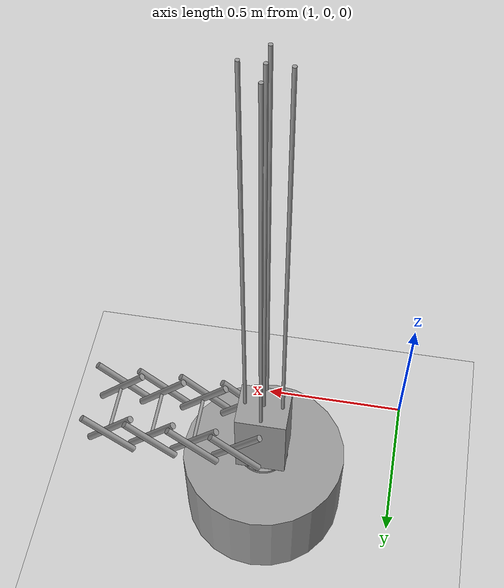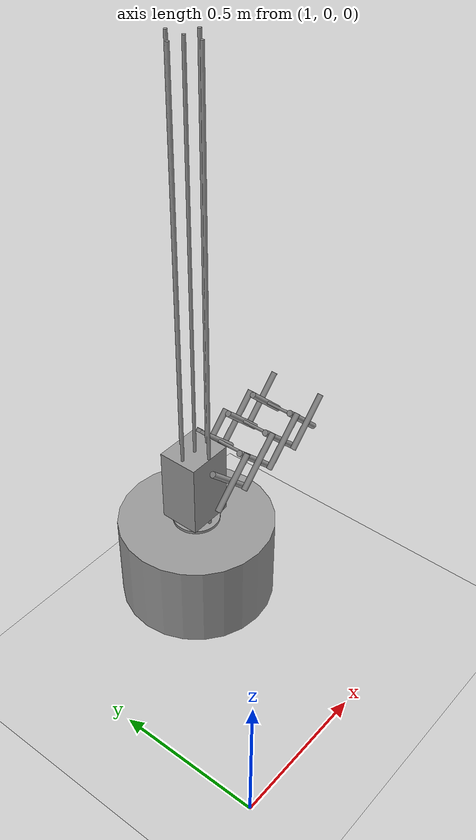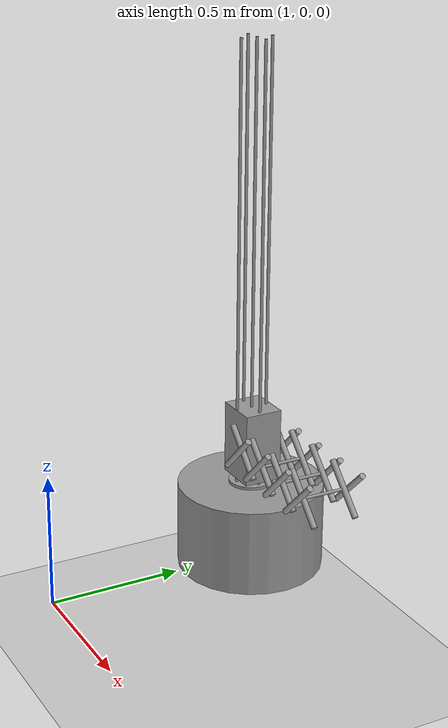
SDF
<?xml version="1.0"?>
<sdf version="1.4">
  <world name="default">
    <include>
      <uri>model://ground_plane</uri>
    </include>

    <include>
      <uri>model://sun</uri>
    </include>

    <include>
      <uri>model:///home/viswa_ns/sim/src/drone_controller/models</uri>
      <name>ArtPark</name>
      <pose>0.0 0.0 0.5 0.0 0.0 0.0</pose>

      <!-- reference to your plugin -->
      <!-- inside the sdf file "full_complete" in /home/suraj/.gazebo/models -->
    </include>

    <plugin name="ros_interface_plugin" filename="librotors_gazebo_ros_interface_plugin.so"/>

    <physics name='default_physics' default='0' type='ode'>
      <gravity>0 0 -9.8066</gravity>
      <ode>
        <solver>
          <type>quick</type>
          <iters>10</iters>
          <sor>1.3</sor>
          <use_dynamic_moi_rescaling>0</use_dynamic_moi_rescaling>
        </solver>
        <constraints>
          <cfm>0</cfm>
          <erp>0.2</erp>
          <contact_max_correcting_vel>100</contact_max_correcting_vel>
          <contact_surface_layer>0.001</contact_surface_layer>
        </constraints>
      </ode>
      <max_step_size>0.002</max_step_size>
      <real_time_factor>1</real_time_factor>
      <real_time_update_rate>700</real_time_update_rate>
      <magnetic_field>6e-06 2.3e-05 -4.2e-05</magnetic_field>
    </physics>

  </world>
</sdf>

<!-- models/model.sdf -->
<sdf version='1.6'>
  <model name='artpark'>
    <link name='link_0'>
      <inertial>
        <mass>1</mass>
        <inertia>
          <ixx>0.145833</ixx>
          <ixy>0</ixy>
          <ixz>0</ixz>
          <iyy>0.145833</iyy>
          <iyz>0</iyz>
          <izz>0.125</izz>
        </inertia>
        <pose frame=''>0 0 0 0 -0 0</pose>
      </inertial>
      <pose frame=''>1.43 0.57 -0.1 0 -0 0</pose>
      <gravity>1</gravity>
      <self_collide>0</self_collide>
      <kinematic>0</kinematic>
      <enable_wind>0</enable_wind>
      <visual name='visual'>
        <pose frame=''>0 0 0 0 -0 0</pose>
        <geometry>
          <cylinder>
            <radius>0.25</radius>
            <length>0.3</length>
          </cylinder>
        </geometry>
        <material>
          <lighting>1</lighting>
          <script>
            <uri>file://media/materials/scripts/gazebo.material</uri>
            <name>Gazebo/Grey</name>
          </script>
          <shader type='pixel'>
            <normal_map>__default__</normal_map>
          </shader>
          <ambient>0.3 0.3 0.3 1</ambient>
          <diffuse>0.7 0.7 0.7 1</diffuse>
          <specular>0.01 0.01 0.01 1</specular>
          <emissive>0 0 0 1</emissive>
        </material>
        <transparency>0</transparency>
        <cast_shadows>1</cast_shadows>
      </visual>
      <collision name='collision'>
        <laser_retro>0</laser_retro>
        <max_contacts>10</max_contacts>
        <pose frame=''>0 0 0 0 -0 0</pose>
        <geometry>
          <cylinder>
            <radius>0.25</radius>
            <length>0.3</length>
          </cylinder>
        </geometry>
        <surface>
          <friction>
            <ode>
              <mu>1</mu>
              <mu2>1</mu2>
              <fdir1>0 0 0</fdir1>
              <slip1>0</slip1>
              <slip2>0</slip2>
            </ode>
            <torsional>
              <coefficient>1</coefficient>
              <patch_radius>0</patch_radius>
              <surface_radius>0</surface_radius>
              <use_patch_radius>1</use_patch_radius>
              <ode>
                <slip>0</slip>
              </ode>
            </torsional>
          </friction>
          <bounce>
            <restitution_coefficient>0</restitution_coefficient>
            <threshold>1e+06</threshold>
          </bounce>
          <contact>
            <collide_without_contact>0</collide_without_contact>
            <collide_without_contact_bitmask>1</collide_without_contact_bitmask>
            <collide_bitmask>1</collide_bitmask>
            <ode>
              <soft_cfm>0</soft_cfm>
              <soft_erp>0.2</soft_erp>
              <kp>1e+13</kp>
              <kd>1</kd>
              <max_vel>0.01</max_vel>
              <min_depth>0</min_depth>
            </ode>
            <bullet>
              <split_impulse>1</split_impulse>
              <split_impulse_penetration_threshold>-0.01</split_impulse_penetration_threshold>
              <soft_cfm>0</soft_cfm>
              <soft_erp>0.2</soft_erp>
              <kp>1e+13</kp>
              <kd>1</kd>
            </bullet>
          </contact>
        </surface>
      </collision>
    </link>
    <link name='link_1'>
      <inertial>
        <mass>1</mass>
        <inertia>
          <ixx>0.166667</ixx>
          <ixy>0</ixy>
          <ixz>0</ixz>
          <iyy>0.166667</iyy>
          <iyz>0</iyz>
          <izz>0.166667</izz>
        </inertia>
        <pose frame=''>0 0 0 0 -0 0</pose>
      </inertial>
      <pose frame=''>1.43 0.57 0.05 0 -0 0</pose>
      <gravity>1</gravity>
      <self_collide>0</self_collide>
      <kinematic>0</kinematic>
      <enable_wind>0</enable_wind>
      <visual name='visual'>
        <pose frame=''>0 0 0 0 -0 0</pose>
        <geometry>
          <mesh>
            <uri>/home/viswa_ns/sim/src/drone_controller/models/spine.stl</uri>
            <scale>0.001 0.001 0.001</scale>
          </mesh>
        </geometry>
        <material>
          <lighting>1</lighting>
          <script>
            <uri>file://media/materials/scripts/gazebo.material</uri>
            <name>Gazebo/Grey</name>
          </script>
          <shader type='pixel'>
            <normal_map>__default__</normal_map>
          </shader>
          <ambient>0.3 0.3 0.3 1</ambient>
          <diffuse>0.7 0.7 0.7 1</diffuse>
          <specular>0.01 0.01 0.01 1</specular>
          <emissive>0 0 0 1</emissive>
        </material>
        <transparency>0</transparency>
        <cast_shadows>1</cast_shadows>
      </visual>
      <collision name='collision'>
        <laser_retro>0</laser_retro>
        <max_contacts>10</max_contacts>
        <pose frame=''>0 0 0 0 -0 0</pose>
        <geometry>
          <mesh>
            <uri>/home/viswa_ns/sim/src/drone_controller/models/spine.stl</uri>
            <scale>0.001 0.001 0.001</scale>
          </mesh>
        </geometry>
        <surface>
          <friction>
            <ode>
              <mu>1</mu>
              <mu2>1</mu2>
              <fdir1>0 0 0</fdir1>
              <slip1>0</slip1>
              <slip2>0</slip2>
            </ode>
            <torsional>
              <coefficient>1</coefficient>
              <patch_radius>0</patch_radius>
              <surface_radius>0</surface_radius>
              <use_patch_radius>1</use_patch_radius>
              <ode>
                <slip>0</slip>
              </ode>
            </torsional>
          </friction>
          <bounce>
            <restitution_coefficient>0</restitution_coefficient>
            <threshold>1e+06</threshold>
          </bounce>
          <contact>
            <collide_without_contact>0</collide_without_contact>
            <collide_without_contact_bitmask>1</collide_without_contact_bitmask>
            <collide_bitmask>1</collide_bitmask>
            <ode>
              <soft_cfm>0</soft_cfm>
              <soft_erp>0.2</soft_erp>
              <kp>1e+13</kp>
              <kd>1</kd>
              <max_vel>0.01</max_vel>
              <min_depth>0</min_depth>
            </ode>
            <bullet>
              <split_impulse>1</split_impulse>
              <split_impulse_penetration_threshold>-0.01</split_impulse_penetration_threshold>
              <soft_cfm>0</soft_cfm>
              <soft_erp>0.2</soft_erp>
              <kp>1e+13</kp>
              <kd>1</kd>
            </bullet>
          </contact>
        </surface>
      </collision>
    </link>
    <link name='link_3'>
      <inertial>
        <mass>1</mass>
        <inertia>
          <ixx>0.166667</ixx>
          <ixy>0</ixy>
          <ixz>0</ixz>
          <iyy>0.166667</iyy>
          <iyz>0</iyz>
          <izz>0.166667</izz>
        </inertia>
        <pose frame=''>0 0 0 0 -0 0</pose>
      </inertial>
      <pose frame=''>1.43 0.575 0.2 0 -0 0</pose>
      <gravity>1</gravity>
      <self_collide>1</self_collide>
      <kinematic>1</kinematic>
      <enable_wind>0</enable_wind>
      <visual name='visual'>
        <pose frame=''>0 0 0 0 -0 0</pose>
        <geometry>
          <box>
            <size>0.15 0.13 0.25</size>
          </box>
        </geometry>
        <material>
          <lighting>1</lighting>
          <script>
            <uri>file://media/materials/scripts/gazebo.material</uri>
            <name>Gazebo/Grey</name>
          </script>
          <shader type='pixel'>
            <normal_map>__default__</normal_map>
          </shader>
          <ambient>0.3 0.3 0.3 1</ambient>
          <diffuse>0.7 0.7 0.7 1</diffuse>
          <specular>0.01 0.01 0.01 1</specular>
          <emissive>0 0 0 1</emissive>
        </material>
        <transparency>0</transparency>
        <cast_shadows>1</cast_shadows>
      </visual>
      <collision name='collision'>
        <laser_retro>0</laser_retro>
        <max_contacts>10</max_contacts>
        <pose frame=''>0 0 0 0 -0 0</pose>
        <geometry>
          <box>
            <size>0.15 0.13 0.25</size>
          </box>
        </geometry>
        <surface>
          <friction>
            <ode>
              <mu>1</mu>
              <mu2>1</mu2>
              <fdir1>0 0 0</fdir1>
              <slip1>0</slip1>
              <slip2>0</slip2>
            </ode>
            <torsional>
              <coefficient>1</coefficient>
              <patch_radius>0</patch_radius>
              <surface_radius>0</surface_radius>
              <use_patch_radius>1</use_patch_radius>
              <ode>
                <slip>0</slip>
              </ode>
            </torsional>
          </friction>
          <bounce>
            <restitution_coefficient>0</restitution_coefficient>
            <threshold>1e+06</threshold>
          </bounce>
          <contact>
            <collide_without_contact>0</collide_without_contact>
            <collide_without_contact_bitmask>1</collide_without_contact_bitmask>
            <collide_bitmask>1</collide_bitmask>
            <ode>
              <soft_cfm>0</soft_cfm>
              <soft_erp>0.2</soft_erp>
              <kp>1e+13</kp>
              <kd>1</kd>
              <max_vel>0.01</max_vel>
              <min_depth>0</min_depth>
            </ode>
            <bullet>
              <split_impulse>1</split_impulse>
              <split_impulse_penetration_threshold>-0.01</split_impulse_penetration_threshold>
              <soft_cfm>0</soft_cfm>
              <soft_erp>0.2</soft_erp>
              <kp>1e+13</kp>
              <kd>1</kd>
            </bullet>
          </contact>
        </surface>
      </collision>
    </link>
    <link name='link_6_clone'>
      <inertial>
        <mass>1</mass>
        <inertia>
          <ixx>0.145833</ixx>
          <ixy>0</ixy>
          <ixz>0</ixz>
          <iyy>0.145833</iyy>
          <iyz>0</iyz>
          <izz>0.125</izz>
        </inertia>
        <pose frame=''>0 0 0 0 -0 0</pose>
      </inertial>
      <pose frame=''>1.5 0.5 0.2 0 -0.785 0</pose>
      <gravity>1</gravity>
      <self_collide>0</self_collide>
      <kinematic>0</kinematic>
      <enable_wind>0</enable_wind>
      <visual name='visual'>
        <pose frame=''>0 0 0 0 -0 0</pose>
        <geometry>
          <cylinder>
            <radius>0.01</radius>
            <length>0.2</length>
          </cylinder>
        </geometry>
        <material>
          <lighting>1</lighting>
          <script>
            <uri>file://media/materials/scripts/gazebo.material</uri>
            <name>Gazebo/Grey</name>
          </script>
          <shader type='pixel'>
            <normal_map>__default__</normal_map>
          </shader>
          <ambient>0.3 0.3 0.3 1</ambient>
          <diffuse>0.7 0.7 0.7 1</diffuse>
          <specular>0.01 0.01 0.01 1</specular>
          <emissive>0 0 0 1</emissive>
        </material>
        <transparency>0</transparency>
        <cast_shadows>1</cast_shadows>
      </visual>
      <collision name='collision'>
        <laser_retro>0</laser_retro>
        <max_contacts>10</max_contacts>
        <pose frame=''>0 0 0 0 -0 0</pose>
        <geometry>
          <cylinder>
            <radius>0.01</radius>
            <length>0.2</length>
          </cylinder>
        </geometry>
        <surface>
          <friction>
            <ode>
              <mu>1</mu>
              <mu2>1</mu2>
              <fdir1>0 0 0</fdir1>
              <slip1>0</slip1>
              <slip2>0</slip2>
            </ode>
            <torsional>
              <coefficient>1</coefficient>
              <patch_radius>0</patch_radius>
              <surface_radius>0</surface_radius>
              <use_patch_radius>1</use_patch_radius>
              <ode>
                <slip>0</slip>
              </ode>
            </torsional>
          </friction>
          <bounce>
            <restitution_coefficient>0</restitution_coefficient>
            <threshold>1e+06</threshold>
          </bounce>
          <contact>
            <collide_without_contact>0</collide_without_contact>
            <collide_without_contact_bitmask>1</collide_without_contact_bitmask>
            <collide_bitmask>1</collide_bitmask>
            <ode>
              <soft_cfm>0</soft_cfm>
              <soft_erp>0.2</soft_erp>
              <kp>1e+13</kp>
              <kd>1</kd>
              <max_vel>0.01</max_vel>
              <min_depth>0</min_depth>
            </ode>
            <bullet>
              <split_impulse>1</split_impulse>
              <split_impulse_penetration_threshold>-0.01</split_impulse_penetration_threshold>
              <soft_cfm>0</soft_cfm>
              <soft_erp>0.2</soft_erp>
              <kp>1e+13</kp>
              <kd>1</kd>
            </bullet>
          </contact>
        </surface>
      </collision>
    </link>
    <link name='link_6_clone_0'>
      <inertial>
        <mass>1</mass>
        <inertia>
          <ixx>0.145833</ixx>
          <ixy>0</ixy>
          <ixz>0</ixz>
          <iyy>0.145833</iyy>
          <iyz>0</iyz>
          <izz>0.125</izz>
        </inertia>
        <pose frame=''>0 0 0 0 -0 0</pose>
      </inertial>
      <pose frame=''>1.6273 0.48 0.2 0 0.785 0</pose>
      <gravity>1</gravity>
      <self_collide>0</self_collide>
      <kinematic>0</kinematic>
      <enable_wind>0</enable_wind>
      <visual name='visual'>
        <pose frame=''>0 0 0 0 -0 0</pose>
        <geometry>
          <cylinder>
            <radius>0.01</radius>
            <length>0.2</length>
          </cylinder>
        </geometry>
        <material>
          <lighting>1</lighting>
          <script>
            <uri>file://media/materials/scripts/gazebo.material</uri>
            <name>Gazebo/Grey</name>
          </script>
          <shader type='pixel'>
            <normal_map>__default__</normal_map>
          </shader>
          <ambient>0.3 0.3 0.3 1</ambient>
          <diffuse>0.7 0.7 0.7 1</diffuse>
          <specular>0.01 0.01 0.01 1</specular>
          <emissive>0 0 0 1</emissive>
        </material>
        <transparency>0</transparency>
        <cast_shadows>1</cast_shadows>
      </visual>
      <collision name='collision'>
        <laser_retro>0</laser_retro>
        <max_contacts>10</max_contacts>
        <pose frame=''>0 0 0 0 -0 0</pose>
        <geometry>
          <cylinder>
            <radius>0.01</radius>
            <length>0.2</length>
          </cylinder>
        </geometry>
        <surface>
          <friction>
            <ode>
              <mu>1</mu>
              <mu2>1</mu2>
              <fdir1>0 0 0</fdir1>
              <slip1>0</slip1>
              <slip2>0</slip2>
            </ode>
            <torsional>
              <coefficient>1</coefficient>
              <patch_radius>0</patch_radius>
              <surface_radius>0</surface_radius>
              <use_patch_radius>1</use_patch_radius>
              <ode>
                <slip>0</slip>
              </ode>
            </torsional>
          </friction>
          <bounce>
            <restitution_coefficient>0</restitution_coefficient>
            <threshold>1e+06</threshold>
          </bounce>
          <contact>
            <collide_without_contact>0</collide_without_contact>
            <collide_without_contact_bitmask>1</collide_without_contact_bitmask>
            <collide_bitmask>1</collide_bitmask>
            <ode>
              <soft_cfm>0</soft_cfm>
              <soft_erp>0.2</soft_erp>
              <kp>1e+13</kp>
              <kd>1</kd>
              <max_vel>0.01</max_vel>
              <min_depth>0</min_depth>
            </ode>
            <bullet>
              <split_impulse>1</split_impulse>
              <split_impulse_penetration_threshold>-0.01</split_impulse_penetration_threshold>
              <soft_cfm>0</soft_cfm>
              <soft_erp>0.2</soft_erp>
              <kp>1e+13</kp>
              <kd>1</kd>
            </bullet>
          </contact>
        </surface>
      </collision>
    </link>
    <link name='link_6_clone_0_clone'>
      <inertial>
        <mass>1</mass>
        <inertia>
          <ixx>0.145833</ixx>
          <ixy>0</ixy>
          <ixz>0</ixz>
          <iyy>0.145833</iyy>
          <iyz>0</iyz>
          <izz>0.125</izz>
        </inertia>
        <pose frame=''>0 0 0 0 -0 0</pose>
      </inertial>
      <pose frame=''>1.755 0.48 0.2 0 0.785 0</pose>
      <gravity>1</gravity>
      <self_collide>0</self_collide>
      <kinematic>0</kinematic>
      <enable_wind>0</enable_wind>
      <visual name='visual'>
        <pose frame=''>0 0 0 0 -0 0</pose>
        <geometry>
          <cylinder>
            <radius>0.01</radius>
            <length>0.2</length>
          </cylinder>
        </geometry>
        <material>
          <lighting>1</lighting>
          <script>
            <uri>file://media/materials/scripts/gazebo.material</uri>
            <name>Gazebo/Grey</name>
          </script>
          <shader type='pixel'>
            <normal_map>__default__</normal_map>
          </shader>
          <ambient>0.3 0.3 0.3 1</ambient>
          <diffuse>0.7 0.7 0.7 1</diffuse>
          <specular>0.01 0.01 0.01 1</specular>
          <emissive>0 0 0 1</emissive>
        </material>
        <transparency>0</transparency>
        <cast_shadows>1</cast_shadows>
      </visual>
      <collision name='collision'>
        <laser_retro>0</laser_retro>
        <max_contacts>10</max_contacts>
        <pose frame=''>0 0 0 0 -0 0</pose>
        <geometry>
          <cylinder>
            <radius>0.01</radius>
            <length>0.2</length>
          </cylinder>
        </geometry>
        <surface>
          <friction>
            <ode>
              <mu>1</mu>
              <mu2>1</mu2>
              <fdir1>0 0 0</fdir1>
              <slip1>0</slip1>
              <slip2>0</slip2>
            </ode>
            <torsional>
              <coefficient>1</coefficient>
              <patch_radius>0</patch_radius>
              <surface_radius>0</surface_radius>
              <use_patch_radius>1</use_patch_radius>
              <ode>
                <slip>0</slip>
              </ode>
            </torsional>
          </friction>
          <bounce>
            <restitution_coefficient>0</restitution_coefficient>
            <threshold>1e+06</threshold>
          </bounce>
          <contact>
            <collide_without_contact>0</collide_without_contact>
            <collide_without_contact_bitmask>1</collide_without_contact_bitmask>
            <collide_bitmask>1</collide_bitmask>
            <ode>
              <soft_cfm>0</soft_cfm>
              <soft_erp>0.2</soft_erp>
              <kp>1e+13</kp>
              <kd>1</kd>
              <max_vel>0.01</max_vel>
              <min_depth>0</min_depth>
            </ode>
            <bullet>
              <split_impulse>1</split_impulse>
              <split_impulse_penetration_threshold>-0.01</split_impulse_penetration_threshold>
              <soft_cfm>0</soft_cfm>
              <soft_erp>0.2</soft_erp>
              <kp>1e+13</kp>
              <kd>1</kd>
            </bullet>
          </contact>
        </surface>
      </collision>
    </link>
    <link name='link_6_clone_0_clone_0'>
      <inertial>
        <mass>1</mass>
        <inertia>
          <ixx>0.145833</ixx>
          <ixy>0</ixy>
          <ixz>0</ixz>
          <iyy>0.145833</iyy>
          <iyz>0</iyz>
          <izz>0.125</izz>
        </inertia>
        <pose frame=''>0 0 0 0 -0 0</pose>
      </inertial>
      <pose frame=''>1.5 0.48 0.2 0 0.785 0</pose>
      <gravity>1</gravity>
      <self_collide>0</self_collide>
      <kinematic>0</kinematic>
      <enable_wind>0</enable_wind>
      <visual name='visual'>
        <pose frame=''>0 0 0 0 -0 0</pose>
        <geometry>
          <cylinder>
            <radius>0.01</radius>
            <length>0.2</length>
          </cylinder>
        </geometry>
        <material>
          <lighting>1</lighting>
          <script>
            <uri>file://media/materials/scripts/gazebo.material</uri>
            <name>Gazebo/Grey</name>
          </script>
          <shader type='pixel'>
            <normal_map>__default__</normal_map>
          </shader>
          <ambient>0.3 0.3 0.3 1</ambient>
          <diffuse>0.7 0.7 0.7 1</diffuse>
          <specular>0.01 0.01 0.01 1</specular>
          <emissive>0 0 0 1</emissive>
        </material>
        <transparency>0</transparency>
        <cast_shadows>1</cast_shadows>
      </visual>
      <collision name='collision'>
        <laser_retro>0</laser_retro>
        <max_contacts>10</max_contacts>
        <pose frame=''>0 0 0 0 -0 0</pose>
        <geometry>
          <cylinder>
            <radius>0.01</radius>
            <length>0.2</length>
          </cylinder>
        </geometry>
        <surface>
          <friction>
            <ode>
              <mu>1</mu>
              <mu2>1</mu2>
              <fdir1>0 0 0</fdir1>
              <slip1>0</slip1>
              <slip2>0</slip2>
            </ode>
            <torsional>
              <coefficient>1</coefficient>
              <patch_radius>0</patch_radius>
              <surface_radius>0</surface_radius>
              <use_patch_radius>1</use_patch_radius>
              <ode>
                <slip>0</slip>
              </ode>
            </torsional>
          </friction>
          <bounce>
            <restitution_coefficient>0</restitution_coefficient>
            <threshold>1e+06</threshold>
          </bounce>
          <contact>
            <collide_without_contact>0</collide_without_contact>
            <collide_without_contact_bitmask>1</collide_without_contact_bitmask>
            <collide_bitmask>1</collide_bitmask>
            <ode>
              <soft_cfm>0</soft_cfm>
              <soft_erp>0.2</soft_erp>
              <kp>1e+13</kp>
              <kd>1</kd>
              <max_vel>0.01</max_vel>
              <min_depth>0</min_depth>
            </ode>
            <bullet>
              <split_impulse>1</split_impulse>
              <split_impulse_penetration_threshold>-0.01</split_impulse_penetration_threshold>
              <soft_cfm>0</soft_cfm>
              <soft_erp>0.2</soft_erp>
              <kp>1e+13</kp>
              <kd>1</kd>
            </bullet>
          </contact>
        </surface>
      </collision>
    </link>
    <link name='link_6_clone_0_clone_clone'>
      <inertial>
        <mass>1</mass>
        <inertia>
          <ixx>0.145833</ixx>
          <ixy>0</ixy>
          <ixz>0</ixz>
          <iyy>0.145833</iyy>
          <iyz>0</iyz>
          <izz>0.125</izz>
        </inertia>
        <pose frame=''>0 0 0 0 -0 0</pose>
      </inertial>
      <pose frame=''>1.8825 0.48 0.2 0 0.785 0</pose>
      <gravity>1</gravity>
      <self_collide>0</self_collide>
      <kinematic>0</kinematic>
      <enable_wind>0</enable_wind>
      <visual name='visual'>
        <pose frame=''>0 0 0 0 -0 0</pose>
        <geometry>
          <cylinder>
            <radius>0.01</radius>
            <length>0.2</length>
          </cylinder>
        </geometry>
        <material>
          <lighting>1</lighting>
          <script>
            <uri>file://media/materials/scripts/gazebo.material</uri>
            <name>Gazebo/Grey</name>
          </script>
          <shader type='pixel'>
            <normal_map>__default__</normal_map>
          </shader>
          <ambient>0.3 0.3 0.3 1</ambient>
          <diffuse>0.7 0.7 0.7 1</diffuse>
          <specular>0.01 0.01 0.01 1</specular>
          <emissive>0 0 0 1</emissive>
        </material>
        <transparency>0</transparency>
        <cast_shadows>1</cast_shadows>
      </visual>
      <collision name='collision'>
        <laser_retro>0</laser_retro>
        <max_contacts>10</max_contacts>
        <pose frame=''>0 0 0 0 -0 0</pose>
        <geometry>
          <cylinder>
            <radius>0.01</radius>
            <length>0.2</length>
          </cylinder>
        </geometry>
        <surface>
          <friction>
            <ode>
              <mu>1</mu>
              <mu2>1</mu2>
              <fdir1>0 0 0</fdir1>
              <slip1>0</slip1>
              <slip2>0</slip2>
            </ode>
            <torsional>
              <coefficient>1</coefficient>
              <patch_radius>0</patch_radius>
              <surface_radius>0</surface_radius>
              <use_patch_radius>1</use_patch_radius>
              <ode>
                <slip>0</slip>
              </ode>
            </torsional>
          </friction>
          <bounce>
            <restitution_coefficient>0</restitution_coefficient>
            <threshold>1e+06</threshold>
          </bounce>
          <contact>
            <collide_without_contact>0</collide_without_contact>
            <collide_without_contact_bitmask>1</collide_without_contact_bitmask>
            <collide_bitmask>1</collide_bitmask>
            <ode>
              <soft_cfm>0</soft_cfm>
              <soft_erp>0.2</soft_erp>
              <kp>1e+13</kp>
              <kd>1</kd>
              <max_vel>0.01</max_vel>
              <min_depth>0</min_depth>
            </ode>
            <bullet>
              <split_impulse>1</split_impulse>
              <split_impulse_penetration_threshold>-0.01</split_impulse_penetration_threshold>
              <soft_cfm>0</soft_cfm>
              <soft_erp>0.2</soft_erp>
              <kp>1e+13</kp>
              <kd>1</kd>
            </bullet>
          </contact>
        </surface>
      </collision>
    </link>
    <link name='link_6_clone_0_clone_clone_0'>
      <inertial>
        <mass>1</mass>
        <inertia>
          <ixx>0.145833</ixx>
          <ixy>0</ixy>
          <ixz>0</ixz>
          <iyy>0.145833</iyy>
          <iyz>0</iyz>
          <izz>0.125</izz>
        </inertia>
        <pose frame=''>0 0 0 0 -0 0</pose>
      </inertial>
      <pose frame=''>1.755 0.67 0.2 0 0.785 0</pose>
      <gravity>1</gravity>
      <self_collide>0</self_collide>
      <kinematic>0</kinematic>
      <enable_wind>0</enable_wind>
      <visual name='visual'>
        <pose frame=''>0 0 0 0 -0 0</pose>
        <geometry>
          <cylinder>
            <radius>0.01</radius>
            <length>0.2</length>
          </cylinder>
        </geometry>
        <material>
          <lighting>1</lighting>
          <script>
            <uri>file://media/materials/scripts/gazebo.material</uri>
            <name>Gazebo/Grey</name>
          </script>
          <shader type='pixel'>
            <normal_map>__default__</normal_map>
          </shader>
          <ambient>0.3 0.3 0.3 1</ambient>
          <diffuse>0.7 0.7 0.7 1</diffuse>
          <specular>0.01 0.01 0.01 1</specular>
          <emissive>0 0 0 1</emissive>
        </material>
        <transparency>0</transparency>
        <cast_shadows>1</cast_shadows>
      </visual>
      <collision name='collision'>
        <laser_retro>0</laser_retro>
        <max_contacts>10</max_contacts>
        <pose frame=''>0 0 0 0 -0 0</pose>
        <geometry>
          <cylinder>
            <radius>0.01</radius>
            <length>0.2</length>
          </cylinder>
        </geometry>
        <surface>
          <friction>
            <ode>
              <mu>1</mu>
              <mu2>1</mu2>
              <fdir1>0 0 0</fdir1>
              <slip1>0</slip1>
              <slip2>0</slip2>
            </ode>
            <torsional>
              <coefficient>1</coefficient>
              <patch_radius>0</patch_radius>
              <surface_radius>0</surface_radius>
              <use_patch_radius>1</use_patch_radius>
              <ode>
                <slip>0</slip>
              </ode>
            </torsional>
          </friction>
          <bounce>
            <restitution_coefficient>0</restitution_coefficient>
            <threshold>1e+06</threshold>
          </bounce>
          <contact>
            <collide_without_contact>0</collide_without_contact>
            <collide_without_contact_bitmask>1</collide_without_contact_bitmask>
            <collide_bitmask>1</collide_bitmask>
            <ode>
              <soft_cfm>0</soft_cfm>
              <soft_erp>0.2</soft_erp>
              <kp>1e+13</kp>
              <kd>1</kd>
              <max_vel>0.01</max_vel>
              <min_depth>0</min_depth>
            </ode>
            <bullet>
              <split_impulse>1</split_impulse>
              <split_impulse_penetration_threshold>-0.01</split_impulse_penetration_threshold>
              <soft_cfm>0</soft_cfm>
              <soft_erp>0.2</soft_erp>
              <kp>1e+13</kp>
              <kd>1</kd>
            </bullet>
          </contact>
        </surface>
      </collision>
    </link>
    <link name='link_6_clone_0_clone_clone_clone'>
      <inertial>
        <mass>1</mass>
        <inertia>
          <ixx>0.145833</ixx>
          <ixy>0</ixy>
          <ixz>0</ixz>
          <iyy>0.145833</iyy>
          <iyz>0</iyz>
          <izz>0.125</izz>
        </inertia>
        <pose frame=''>0 0 0 0 -0 0</pose>
      </inertial>
      <pose frame=''>1.8825 0.67 0.2 0 0.785 0</pose>
      <gravity>1</gravity>
      <self_collide>0</self_collide>
      <kinematic>0</kinematic>
      <enable_wind>0</enable_wind>
      <visual name='visual'>
        <pose frame=''>0 0 0 0 -0 0</pose>
        <geometry>
          <cylinder>
            <radius>0.01</radius>
            <length>0.2</length>
          </cylinder>
        </geometry>
        <material>
          <lighting>1</lighting>
          <script>
            <uri>file://media/materials/scripts/gazebo.material</uri>
            <name>Gazebo/Grey</name>
          </script>
          <shader type='pixel'>
            <normal_map>__default__</normal_map>
          </shader>
          <ambient>0.3 0.3 0.3 1</ambient>
          <diffuse>0.7 0.7 0.7 1</diffuse>
          <specular>0.01 0.01 0.01 1</specular>
          <emissive>0 0 0 1</emissive>
        </material>
        <transparency>0</transparency>
        <cast_shadows>1</cast_shadows>
      </visual>
      <collision name='collision'>
        <laser_retro>0</laser_retro>
        <max_contacts>10</max_contacts>
        <pose frame=''>0 0 0 0 -0 0</pose>
        <geometry>
          <cylinder>
            <radius>0.01</radius>
            <length>0.2</length>
          </cylinder>
        </geometry>
        <surface>
          <friction>
            <ode>
              <mu>1</mu>
              <mu2>1</mu2>
              <fdir1>0 0 0</fdir1>
              <slip1>0</slip1>
              <slip2>0</slip2>
            </ode>
            <torsional>
              <coefficient>1</coefficient>
              <patch_radius>0</patch_radius>
              <surface_radius>0</surface_radius>
              <use_patch_radius>1</use_patch_radius>
              <ode>
                <slip>0</slip>
              </ode>
            </torsional>
          </friction>
          <bounce>
            <restitution_coefficient>0</restitution_coefficient>
            <threshold>1e+06</threshold>
          </bounce>
          <contact>
            <collide_without_contact>0</collide_without_contact>
            <collide_without_contact_bitmask>1</collide_without_contact_bitmask>
            <collide_bitmask>1</collide_bitmask>
            <ode>
              <soft_cfm>0</soft_cfm>
              <soft_erp>0.2</soft_erp>
              <kp>1e+13</kp>
              <kd>1</kd>
              <max_vel>0.01</max_vel>
              <min_depth>0</min_depth>
            </ode>
            <bullet>
              <split_impulse>1</split_impulse>
              <split_impulse_penetration_threshold>-0.01</split_impulse_penetration_threshold>
              <soft_cfm>0</soft_cfm>
              <soft_erp>0.2</soft_erp>
              <kp>1e+13</kp>
              <kd>1</kd>
            </bullet>
          </contact>
        </surface>
      </collision>
    </link>
    <link name='link_6_clone_clone'>
      <inertial>
        <mass>1</mass>
        <inertia>
          <ixx>0.145833</ixx>
          <ixy>0</ixy>
          <ixz>0</ixz>
          <iyy>0.145833</iyy>
          <iyz>0</iyz>
          <izz>0.125</izz>
        </inertia>
        <pose frame=''>0 0 0 0 -0 0</pose>
      </inertial>
      <pose frame=''>1.6273 0.5 0.2 0 -0.785 0</pose>
      <gravity>1</gravity>
      <self_collide>0</self_collide>
      <kinematic>0</kinematic>
      <enable_wind>0</enable_wind>
      <visual name='visual'>
        <pose frame=''>0 0 0 0 -0 0</pose>
        <geometry>
          <cylinder>
            <radius>0.01</radius>
            <length>0.2</length>
          </cylinder>
        </geometry>
        <material>
          <lighting>1</lighting>
          <script>
            <uri>file://media/materials/scripts/gazebo.material</uri>
            <name>Gazebo/Grey</name>
          </script>
          <shader type='pixel'>
            <normal_map>__default__</normal_map>
          </shader>
          <ambient>0.3 0.3 0.3 1</ambient>
          <diffuse>0.7 0.7 0.7 1</diffuse>
          <specular>0.01 0.01 0.01 1</specular>
          <emissive>0 0 0 1</emissive>
        </material>
        <transparency>0</transparency>
        <cast_shadows>1</cast_shadows>
      </visual>
      <collision name='collision'>
        <laser_retro>0</laser_retro>
        <max_contacts>10</max_contacts>
        <pose frame=''>0 0 0 0 -0 0</pose>
        <geometry>
          <cylinder>
            <radius>0.01</radius>
            <length>0.2</length>
          </cylinder>
        </geometry>
        <surface>
          <friction>
            <ode>
              <mu>1</mu>
              <mu2>1</mu2>
              <fdir1>0 0 0</fdir1>
              <slip1>0</slip1>
              <slip2>0</slip2>
            </ode>
            <torsional>
              <coefficient>1</coefficient>
              <patch_radius>0</patch_radius>
              <surface_radius>0</surface_radius>
              <use_patch_radius>1</use_patch_radius>
              <ode>
                <slip>0</slip>
              </ode>
            </torsional>
          </friction>
          <bounce>
            <restitution_coefficient>0</restitution_coefficient>
            <threshold>1e+06</threshold>
          </bounce>
          <contact>
            <collide_without_contact>0</collide_without_contact>
            <collide_without_contact_bitmask>1</collide_without_contact_bitmask>
            <collide_bitmask>1</collide_bitmask>
            <ode>
              <soft_cfm>0</soft_cfm>
              <soft_erp>0.2</soft_erp>
              <kp>1e+13</kp>
              <kd>1</kd>
              <max_vel>0.01</max_vel>
              <min_depth>0</min_depth>
            </ode>
            <bullet>
              <split_impulse>1</split_impulse>
              <split_impulse_penetration_threshold>-0.01</split_impulse_penetration_threshold>
              <soft_cfm>0</soft_cfm>
              <soft_erp>0.2</soft_erp>
              <kp>1e+13</kp>
              <kd>1</kd>
            </bullet>
          </contact>
        </surface>
      </collision>
    </link>
    <link name='link_6_clone_clone_0'>
      <inertial>
        <mass>1</mass>
        <inertia>
          <ixx>0.145833</ixx>
          <ixy>0</ixy>
          <ixz>0</ixz>
          <iyy>0.145833</iyy>
          <iyz>0</iyz>
          <izz>0.125</izz>
        </inertia>
        <pose frame=''>0 0 0 0 -0 0</pose>
      </inertial>
      <pose frame=''>1.5 0.65 0.2 0 -0.785 0</pose>
      <gravity>1</gravity>
      <self_collide>0</self_collide>
      <kinematic>0</kinematic>
      <enable_wind>0</enable_wind>
      <visual name='visual'>
        <pose frame=''>0 0 0 0 -0 0</pose>
        <geometry>
          <cylinder>
            <radius>0.01</radius>
            <length>0.2</length>
          </cylinder>
        </geometry>
        <material>
          <lighting>1</lighting>
          <script>
            <uri>file://media/materials/scripts/gazebo.material</uri>
            <name>Gazebo/Grey</name>
          </script>
          <shader type='pixel'>
            <normal_map>__default__</normal_map>
          </shader>
          <ambient>0.3 0.3 0.3 1</ambient>
          <diffuse>0.7 0.7 0.7 1</diffuse>
          <specular>0.01 0.01 0.01 1</specular>
          <emissive>0 0 0 1</emissive>
        </material>
        <transparency>0</transparency>
        <cast_shadows>1</cast_shadows>
      </visual>
      <collision name='collision'>
        <laser_retro>0</laser_retro>
        <max_contacts>10</max_contacts>
        <pose frame=''>0 0 0 0 -0 0</pose>
        <geometry>
          <cylinder>
            <radius>0.01</radius>
            <length>0.2</length>
          </cylinder>
        </geometry>
        <surface>
          <friction>
            <ode>
              <mu>1</mu>
              <mu2>1</mu2>
              <fdir1>0 0 0</fdir1>
              <slip1>0</slip1>
              <slip2>0</slip2>
            </ode>
            <torsional>
              <coefficient>1</coefficient>
              <patch_radius>0</patch_radius>
              <surface_radius>0</surface_radius>
              <use_patch_radius>1</use_patch_radius>
              <ode>
                <slip>0</slip>
              </ode>
            </torsional>
          </friction>
          <bounce>
            <restitution_coefficient>0</restitution_coefficient>
            <threshold>1e+06</threshold>
          </bounce>
          <contact>
            <collide_without_contact>0</collide_without_contact>
            <collide_without_contact_bitmask>1</collide_without_contact_bitmask>
            <collide_bitmask>1</collide_bitmask>
            <ode>
              <soft_cfm>0</soft_cfm>
              <soft_erp>0.2</soft_erp>
              <kp>1e+13</kp>
              <kd>1</kd>
              <max_vel>0.01</max_vel>
              <min_depth>0</min_depth>
            </ode>
            <bullet>
              <split_impulse>1</split_impulse>
              <split_impulse_penetration_threshold>-0.01</split_impulse_penetration_threshold>
              <soft_cfm>0</soft_cfm>
              <soft_erp>0.2</soft_erp>
              <kp>1e+13</kp>
              <kd>1</kd>
            </bullet>
          </contact>
        </surface>
      </collision>
    </link>
    <link name='link_6_clone_clone_0_clone'>
      <inertial>
        <mass>1</mass>
        <inertia>
          <ixx>0.145833</ixx>
          <ixy>0</ixy>
          <ixz>0</ixz>
          <iyy>0.145833</iyy>
          <iyz>0</iyz>
          <izz>0.125</izz>
        </inertia>
        <pose frame=''>0 0 0 0 -0 0</pose>
      </inertial>
      <pose frame=''>1.5 0.67 0.2 0 0.785 0</pose>
      <gravity>1</gravity>
      <self_collide>0</self_collide>
      <kinematic>0</kinematic>
      <enable_wind>0</enable_wind>
      <visual name='visual'>
        <pose frame=''>0 0 0 0 -0 0</pose>
        <geometry>
          <cylinder>
            <radius>0.01</radius>
            <length>0.2</length>
          </cylinder>
        </geometry>
        <material>
          <lighting>1</lighting>
          <script>
            <uri>file://media/materials/scripts/gazebo.material</uri>
            <name>Gazebo/Grey</name>
          </script>
          <shader type='pixel'>
            <normal_map>__default__</normal_map>
          </shader>
          <ambient>0.3 0.3 0.3 1</ambient>
          <diffuse>0.7 0.7 0.7 1</diffuse>
          <specular>0.01 0.01 0.01 1</specular>
          <emissive>0 0 0 1</emissive>
        </material>
        <transparency>0</transparency>
        <cast_shadows>1</cast_shadows>
      </visual>
      <collision name='collision'>
        <laser_retro>0</laser_retro>
        <max_contacts>10</max_contacts>
        <pose frame=''>0 0 0 0 -0 0</pose>
        <geometry>
          <cylinder>
            <radius>0.01</radius>
            <length>0.2</length>
          </cylinder>
        </geometry>
        <surface>
          <friction>
            <ode>
              <mu>1</mu>
              <mu2>1</mu2>
              <fdir1>0 0 0</fdir1>
              <slip1>0</slip1>
              <slip2>0</slip2>
            </ode>
            <torsional>
              <coefficient>1</coefficient>
              <patch_radius>0</patch_radius>
              <surface_radius>0</surface_radius>
              <use_patch_radius>1</use_patch_radius>
              <ode>
                <slip>0</slip>
              </ode>
            </torsional>
          </friction>
          <bounce>
            <restitution_coefficient>0</restitution_coefficient>
            <threshold>1e+06</threshold>
          </bounce>
          <contact>
            <collide_without_contact>0</collide_without_contact>
            <collide_without_contact_bitmask>1</collide_without_contact_bitmask>
            <collide_bitmask>1</collide_bitmask>
            <ode>
              <soft_cfm>0</soft_cfm>
              <soft_erp>0.2</soft_erp>
              <kp>1e+13</kp>
              <kd>1</kd>
              <max_vel>0.01</max_vel>
              <min_depth>0</min_depth>
            </ode>
            <bullet>
              <split_impulse>1</split_impulse>
              <split_impulse_penetration_threshold>-0.01</split_impulse_penetration_threshold>
              <soft_cfm>0</soft_cfm>
              <soft_erp>0.2</soft_erp>
              <kp>1e+13</kp>
              <kd>1</kd>
            </bullet>
          </contact>
        </surface>
      </collision>
    </link>
    <link name='link_6_clone_clone_0_clone_clone'>
      <inertial>
        <mass>1</mass>
        <inertia>
          <ixx>0.145833</ixx>
          <ixy>0</ixy>
          <ixz>0</ixz>
          <iyy>0.145833</iyy>
          <iyz>0</iyz>
          <izz>0.125</izz>
        </inertia>
        <pose frame=''>0 0 0 0 -0 0</pose>
      </inertial>
      <pose frame=''>1.6273 0.67 0.2 0 0.785 0</pose>
      <gravity>1</gravity>
      <self_collide>0</self_collide>
      <kinematic>0</kinematic>
      <enable_wind>0</enable_wind>
      <visual name='visual'>
        <pose frame=''>0 0 0 0 -0 0</pose>
        <geometry>
          <cylinder>
            <radius>0.01</radius>
            <length>0.2</length>
          </cylinder>
        </geometry>
        <material>
          <lighting>1</lighting>
          <script>
            <uri>file://media/materials/scripts/gazebo.material</uri>
            <name>Gazebo/Grey</name>
          </script>
          <shader type='pixel'>
            <normal_map>__default__</normal_map>
          </shader>
          <ambient>0.3 0.3 0.3 1</ambient>
          <diffuse>0.7 0.7 0.7 1</diffuse>
          <specular>0.01 0.01 0.01 1</specular>
          <emissive>0 0 0 1</emissive>
        </material>
        <transparency>0</transparency>
        <cast_shadows>1</cast_shadows>
      </visual>
      <collision name='collision'>
        <laser_retro>0</laser_retro>
        <max_contacts>10</max_contacts>
        <pose frame=''>0 0 0 0 -0 0</pose>
        <geometry>
          <cylinder>
            <radius>0.01</radius>
            <length>0.2</length>
          </cylinder>
        </geometry>
        <surface>
          <friction>
            <ode>
              <mu>1</mu>
              <mu2>1</mu2>
              <fdir1>0 0 0</fdir1>
              <slip1>0</slip1>
              <slip2>0</slip2>
            </ode>
            <torsional>
              <coefficient>1</coefficient>
              <patch_radius>0</patch_radius>
              <surface_radius>0</surface_radius>
              <use_patch_radius>1</use_patch_radius>
              <ode>
                <slip>0</slip>
              </ode>
            </torsional>
          </friction>
          <bounce>
            <restitution_coefficient>0</restitution_coefficient>
            <threshold>1e+06</threshold>
          </bounce>
          <contact>
            <collide_without_contact>0</collide_without_contact>
            <collide_without_contact_bitmask>1</collide_without_contact_bitmask>
            <collide_bitmask>1</collide_bitmask>
            <ode>
              <soft_cfm>0</soft_cfm>
              <soft_erp>0.2</soft_erp>
              <kp>1e+13</kp>
              <kd>1</kd>
              <max_vel>0.01</max_vel>
              <min_depth>0</min_depth>
            </ode>
            <bullet>
              <split_impulse>1</split_impulse>
              <split_impulse_penetration_threshold>-0.01</split_impulse_penetration_threshold>
              <soft_cfm>0</soft_cfm>
              <soft_erp>0.2</soft_erp>
              <kp>1e+13</kp>
              <kd>1</kd>
            </bullet>
          </contact>
        </surface>
      </collision>
    </link>
    <link name='link_6_clone_clone_0_clone_clone_0'>
      <inertial>
        <mass>1</mass>
        <inertia>
          <ixx>0.145833</ixx>
          <ixy>0</ixy>
          <ixz>0</ixz>
          <iyy>0.145833</iyy>
          <iyz>0</iyz>
          <izz>0.125</izz>
        </inertia>
        <pose frame=''>0 0 0 0 -0 0</pose>
      </inertial>
      <pose frame=''>1.5 0.575 0.2 1.57 -0 0</pose>
      <gravity>1</gravity>
      <self_collide>0</self_collide>
      <kinematic>0</kinematic>
      <enable_wind>0</enable_wind>
      <visual name='visual'>
        <pose frame=''>0 0 0 0 -0 0</pose>
        <geometry>
          <cylinder>
            <radius>0.005</radius>
            <length>0.15</length>
          </cylinder>
        </geometry>
        <material>
          <lighting>1</lighting>
          <script>
            <uri>file://media/materials/scripts/gazebo.material</uri>
            <name>Gazebo/Grey</name>
          </script>
          <shader type='pixel'>
            <normal_map>__default__</normal_map>
          </shader>
          <ambient>0.3 0.3 0.3 1</ambient>
          <diffuse>0.7 0.7 0.7 1</diffuse>
          <specular>0.01 0.01 0.01 1</specular>
          <emissive>0 0 0 1</emissive>
        </material>
        <transparency>0</transparency>
        <cast_shadows>1</cast_shadows>
      </visual>
      <collision name='collision'>
        <laser_retro>0</laser_retro>
        <max_contacts>10</max_contacts>
        <pose frame=''>0 0 0 0 -0 0</pose>
        <geometry>
          <cylinder>
            <radius>0.005</radius>
            <length>0.15</length>
          </cylinder>
        </geometry>
        <surface>
          <friction>
            <ode>
              <mu>1</mu>
              <mu2>1</mu2>
              <fdir1>0 0 0</fdir1>
              <slip1>0</slip1>
              <slip2>0</slip2>
            </ode>
            <torsional>
              <coefficient>1</coefficient>
              <patch_radius>0</patch_radius>
              <surface_radius>0</surface_radius>
              <use_patch_radius>1</use_patch_radius>
              <ode>
                <slip>0</slip>
              </ode>
            </torsional>
          </friction>
          <bounce>
            <restitution_coefficient>0</restitution_coefficient>
            <threshold>1e+06</threshold>
          </bounce>
          <contact>
            <collide_without_contact>0</collide_without_contact>
            <collide_without_contact_bitmask>1</collide_without_contact_bitmask>
            <collide_bitmask>1</collide_bitmask>
            <ode>
              <soft_cfm>0</soft_cfm>
              <soft_erp>0.2</soft_erp>
              <kp>1e+13</kp>
              <kd>1</kd>
              <max_vel>0.01</max_vel>
              <min_depth>0</min_depth>
            </ode>
            <bullet>
              <split_impulse>1</split_impulse>
              <split_impulse_penetration_threshold>-0.01</split_impulse_penetration_threshold>
              <soft_cfm>0</soft_cfm>
              <soft_erp>0.2</soft_erp>
              <kp>1e+13</kp>
              <kd>1</kd>
            </bullet>
          </contact>
        </surface>
      </collision>
    </link>
    <link name='link_6_clone_clone_0_clone_clone_0_clone'>
      <inertial>
        <mass>1</mass>
        <inertia>
          <ixx>0.145833</ixx>
          <ixy>0</ixy>
          <ixz>0</ixz>
          <iyy>0.145833</iyy>
          <iyz>0</iyz>
          <izz>0.125</izz>
        </inertia>
        <pose frame=''>0 0 0 0 -0 0</pose>
      </inertial>
      <pose frame=''>1.6273 0.575 0.2 1.57 -0 0</pose>
      <gravity>1</gravity>
      <self_collide>0</self_collide>
      <kinematic>0</kinematic>
      <enable_wind>0</enable_wind>
      <visual name='visual'>
        <pose frame=''>0 0 0 0 -0 0</pose>
        <geometry>
          <cylinder>
            <radius>0.005</radius>
            <length>0.15</length>
          </cylinder>
        </geometry>
        <material>
          <lighting>1</lighting>
          <script>
            <uri>file://media/materials/scripts/gazebo.material</uri>
            <name>Gazebo/Grey</name>
          </script>
          <shader type='pixel'>
            <normal_map>__default__</normal_map>
          </shader>
          <ambient>0.3 0.3 0.3 1</ambient>
          <diffuse>0.7 0.7 0.7 1</diffuse>
          <specular>0.01 0.01 0.01 1</specular>
          <emissive>0 0 0 1</emissive>
        </material>
        <transparency>0</transparency>
        <cast_shadows>1</cast_shadows>
      </visual>
      <collision name='collision'>
        <laser_retro>0</laser_retro>
        <max_contacts>10</max_contacts>
        <pose frame=''>0 0 0 0 -0 0</pose>
        <geometry>
          <cylinder>
            <radius>0.005</radius>
            <length>0.15</length>
          </cylinder>
        </geometry>
        <surface>
          <friction>
            <ode>
              <mu>1</mu>
              <mu2>1</mu2>
              <fdir1>0 0 0</fdir1>
              <slip1>0</slip1>
              <slip2>0</slip2>
            </ode>
            <torsional>
              <coefficient>1</coefficient>
              <patch_radius>0</patch_radius>
              <surface_radius>0</surface_radius>
              <use_patch_radius>1</use_patch_radius>
              <ode>
                <slip>0</slip>
              </ode>
            </torsional>
          </friction>
          <bounce>
            <restitution_coefficient>0</restitution_coefficient>
            <threshold>1e+06</threshold>
          </bounce>
          <contact>
            <collide_without_contact>0</collide_without_contact>
            <collide_without_contact_bitmask>1</collide_without_contact_bitmask>
            <collide_bitmask>1</collide_bitmask>
            <ode>
              <soft_cfm>0</soft_cfm>
              <soft_erp>0.2</soft_erp>
              <kp>1e+13</kp>
              <kd>1</kd>
              <max_vel>0.01</max_vel>
              <min_depth>0</min_depth>
            </ode>
            <bullet>
              <split_impulse>1</split_impulse>
              <split_impulse_penetration_threshold>-0.01</split_impulse_penetration_threshold>
              <soft_cfm>0</soft_cfm>
              <soft_erp>0.2</soft_erp>
              <kp>1e+13</kp>
              <kd>1</kd>
            </bullet>
          </contact>
        </surface>
      </collision>
    </link>
    <link name='link_6_clone_clone_0_clone_clone_0_clone_0'>
      <inertial>
        <mass>1</mass>
        <inertia>
          <ixx>0.145833</ixx>
          <ixy>0</ixy>
          <ixz>0</ixz>
          <iyy>0.145833</iyy>
          <iyz>0</iyz>
          <izz>0.125</izz>
        </inertia>
        <pose frame=''>0 0 0 0 -0 0</pose>
      </inertial>
      <pose frame=''>1.755 0.575 0.2 1.57 -0 0</pose>
      <gravity>1</gravity>
      <self_collide>0</self_collide>
      <kinematic>0</kinematic>
      <enable_wind>0</enable_wind>
      <visual name='visual'>
        <pose frame=''>0 0 0 0 -0 0</pose>
        <geometry>
          <cylinder>
            <radius>0.005</radius>
            <length>0.15</length>
          </cylinder>
        </geometry>
        <material>
          <lighting>1</lighting>
          <script>
            <uri>file://media/materials/scripts/gazebo.material</uri>
            <name>Gazebo/Grey</name>
          </script>
          <shader type='pixel'>
            <normal_map>__default__</normal_map>
          </shader>
          <ambient>0.3 0.3 0.3 1</ambient>
          <diffuse>0.7 0.7 0.7 1</diffuse>
          <specular>0.01 0.01 0.01 1</specular>
          <emissive>0 0 0 1</emissive>
        </material>
        <transparency>0</transparency>
        <cast_shadows>1</cast_shadows>
      </visual>
      <collision name='collision'>
        <laser_retro>0</laser_retro>
        <max_contacts>10</max_contacts>
        <pose frame=''>0 0 0 0 -0 0</pose>
        <geometry>
          <cylinder>
            <radius>0.005</radius>
            <length>0.15</length>
          </cylinder>
        </geometry>
        <surface>
          <friction>
            <ode>
              <mu>1</mu>
              <mu2>1</mu2>
              <fdir1>0 0 0</fdir1>
              <slip1>0</slip1>
              <slip2>0</slip2>
            </ode>
            <torsional>
              <coefficient>1</coefficient>
              <patch_radius>0</patch_radius>
              <surface_radius>0</surface_radius>
              <use_patch_radius>1</use_patch_radius>
              <ode>
                <slip>0</slip>
              </ode>
            </torsional>
          </friction>
          <bounce>
            <restitution_coefficient>0</restitution_coefficient>
            <threshold>1e+06</threshold>
          </bounce>
          <contact>
            <collide_without_contact>0</collide_without_contact>
            <collide_without_contact_bitmask>1</collide_without_contact_bitmask>
            <collide_bitmask>1</collide_bitmask>
            <ode>
              <soft_cfm>0</soft_cfm>
              <soft_erp>0.2</soft_erp>
              <kp>1e+13</kp>
              <kd>1</kd>
              <max_vel>0.01</max_vel>
              <min_depth>0</min_depth>
            </ode>
            <bullet>
              <split_impulse>1</split_impulse>
              <split_impulse_penetration_threshold>-0.01</split_impulse_penetration_threshold>
              <soft_cfm>0</soft_cfm>
              <soft_erp>0.2</soft_erp>
              <kp>1e+13</kp>
              <kd>1</kd>
            </bullet>
          </contact>
        </surface>
      </collision>
    </link>
    <link name='link_6_clone_clone_0_clone_clone_0_clone_1'>
      <inertial>
        <mass>1</mass>
        <inertia>
          <ixx>0.145833</ixx>
          <ixy>0</ixy>
          <ixz>0</ixz>
          <iyy>0.145833</iyy>
          <iyz>0</iyz>
          <izz>0.125</izz>
        </inertia>
        <pose frame=''>0 0 0 0 -0 0</pose>
      </inertial>
      <pose frame=''>1.8825 0.575 0.2 1.57 -0 0</pose>
      <gravity>1</gravity>
      <self_collide>0</self_collide>
      <kinematic>0</kinematic>
      <enable_wind>0</enable_wind>
      <visual name='visual'>
        <pose frame=''>0 0 0 0 -0 0</pose>
        <geometry>
          <cylinder>
            <radius>0.005</radius>
            <length>0.15</length>
          </cylinder>
        </geometry>
        <material>
          <lighting>1</lighting>
          <script>
            <uri>file://media/materials/scripts/gazebo.material</uri>
            <name>Gazebo/Grey</name>
          </script>
          <shader type='pixel'>
            <normal_map>__default__</normal_map>
          </shader>
          <ambient>0.3 0.3 0.3 1</ambient>
          <diffuse>0.7 0.7 0.7 1</diffuse>
          <specular>0.01 0.01 0.01 1</specular>
          <emissive>0 0 0 1</emissive>
        </material>
        <transparency>0</transparency>
        <cast_shadows>1</cast_shadows>
      </visual>
      <collision name='collision'>
        <laser_retro>0</laser_retro>
        <max_contacts>10</max_contacts>
        <pose frame=''>0 0 0 0 -0 0</pose>
        <geometry>
          <cylinder>
            <radius>0.005</radius>
            <length>0.15</length>
          </cylinder>
        </geometry>
        <surface>
          <friction>
            <ode>
              <mu>1</mu>
              <mu2>1</mu2>
              <fdir1>0 0 0</fdir1>
              <slip1>0</slip1>
              <slip2>0</slip2>
            </ode>
            <torsional>
              <coefficient>1</coefficient>
              <patch_radius>0</patch_radius>
              <surface_radius>0</surface_radius>
              <use_patch_radius>1</use_patch_radius>
              <ode>
                <slip>0</slip>
              </ode>
            </torsional>
          </friction>
          <bounce>
            <restitution_coefficient>0</restitution_coefficient>
            <threshold>1e+06</threshold>
          </bounce>
          <contact>
            <collide_without_contact>0</collide_without_contact>
            <collide_without_contact_bitmask>1</collide_without_contact_bitmask>
            <collide_bitmask>1</collide_bitmask>
            <ode>
              <soft_cfm>0</soft_cfm>
              <soft_erp>0.2</soft_erp>
              <kp>1e+13</kp>
              <kd>1</kd>
              <max_vel>0.01</max_vel>
              <min_depth>0</min_depth>
            </ode>
            <bullet>
              <split_impulse>1</split_impulse>
              <split_impulse_penetration_threshold>-0.01</split_impulse_penetration_threshold>
              <soft_cfm>0</soft_cfm>
              <soft_erp>0.2</soft_erp>
              <kp>1e+13</kp>
              <kd>1</kd>
            </bullet>
          </contact>
        </surface>
      </collision>
    </link>
    <link name='link_6_clone_clone_0_clone_clone_clone'>
      <inertial>
        <mass>1</mass>
        <inertia>
          <ixx>0.145833</ixx>
          <ixy>0</ixy>
          <ixz>0</ixz>
          <iyy>0.145833</iyy>
          <iyz>0</iyz>
          <izz>0.125</izz>
        </inertia>
        <pose frame=''>0 0 0 0 -0 0</pose>
      </inertial>
      <pose frame=''>1.6273 0.65 0.2 0 -0.785 0</pose>
      <gravity>1</gravity>
      <self_collide>0</self_collide>
      <kinematic>0</kinematic>
      <enable_wind>0</enable_wind>
      <visual name='visual'>
        <pose frame=''>0 0 0 0 -0 0</pose>
        <geometry>
          <cylinder>
            <radius>0.01</radius>
            <length>0.2</length>
          </cylinder>
        </geometry>
        <material>
          <lighting>1</lighting>
          <script>
            <uri>file://media/materials/scripts/gazebo.material</uri>
            <name>Gazebo/Grey</name>
          </script>
          <shader type='pixel'>
            <normal_map>__default__</normal_map>
          </shader>
          <ambient>0.3 0.3 0.3 1</ambient>
          <diffuse>0.7 0.7 0.7 1</diffuse>
          <specular>0.01 0.01 0.01 1</specular>
          <emissive>0 0 0 1</emissive>
        </material>
        <transparency>0</transparency>
        <cast_shadows>1</cast_shadows>
      </visual>
      <collision name='collision'>
        <laser_retro>0</laser_retro>
        <max_contacts>10</max_contacts>
        <pose frame=''>0 0 0 0 -0 0</pose>
        <geometry>
          <cylinder>
            <radius>0.01</radius>
            <length>0.2</length>
          </cylinder>
        </geometry>
        <surface>
          <friction>
            <ode>
              <mu>1</mu>
              <mu2>1</mu2>
              <fdir1>0 0 0</fdir1>
              <slip1>0</slip1>
              <slip2>0</slip2>
            </ode>
            <torsional>
              <coefficient>1</coefficient>
              <patch_radius>0</patch_radius>
              <surface_radius>0</surface_radius>
              <use_patch_radius>1</use_patch_radius>
              <ode>
                <slip>0</slip>
              </ode>
            </torsional>
          </friction>
          <bounce>
            <restitution_coefficient>0</restitution_coefficient>
            <threshold>1e+06</threshold>
          </bounce>
          <contact>
            <collide_without_contact>0</collide_without_contact>
            <collide_without_contact_bitmask>1</collide_without_contact_bitmask>
            <collide_bitmask>1</collide_bitmask>
            <ode>
              <soft_cfm>0</soft_cfm>
              <soft_erp>0.2</soft_erp>
              <kp>1e+13</kp>
              <kd>1</kd>
              <max_vel>0.01</max_vel>
              <min_depth>0</min_depth>
            </ode>
            <bullet>
              <split_impulse>1</split_impulse>
              <split_impulse_penetration_threshold>-0.01</split_impulse_penetration_threshold>
              <soft_cfm>0</soft_cfm>
              <soft_erp>0.2</soft_erp>
              <kp>1e+13</kp>
              <kd>1</kd>
            </bullet>
          </contact>
        </surface>
      </collision>
    </link>
    <link name='link_6_clone_clone_clone'>
      <inertial>
        <mass>1</mass>
        <inertia>
          <ixx>0.145833</ixx>
          <ixy>0</ixy>
          <ixz>0</ixz>
          <iyy>0.145833</iyy>
          <iyz>0</iyz>
          <izz>0.125</izz>
        </inertia>
        <pose frame=''>0 0 0 0 -0 0</pose>
      </inertial>
      <pose frame=''>1.755 0.5 0.2 0 -0.785 0</pose>
      <gravity>1</gravity>
      <self_collide>0</self_collide>
      <kinematic>0</kinematic>
      <enable_wind>0</enable_wind>
      <visual name='visual'>
        <pose frame=''>0 0 0 0 -0 0</pose>
        <geometry>
          <cylinder>
            <radius>0.01</radius>
            <length>0.2</length>
          </cylinder>
        </geometry>
        <material>
          <lighting>1</lighting>
          <script>
            <uri>file://media/materials/scripts/gazebo.material</uri>
            <name>Gazebo/Grey</name>
          </script>
          <shader type='pixel'>
            <normal_map>__default__</normal_map>
          </shader>
          <ambient>0.3 0.3 0.3 1</ambient>
          <diffuse>0.7 0.7 0.7 1</diffuse>
          <specular>0.01 0.01 0.01 1</specular>
          <emissive>0 0 0 1</emissive>
        </material>
        <transparency>0</transparency>
        <cast_shadows>1</cast_shadows>
      </visual>
      <collision name='collision'>
        <laser_retro>0</laser_retro>
        <max_contacts>10</max_contacts>
        <pose frame=''>0 0 0 0 -0 0</pose>
        <geometry>
          <cylinder>
            <radius>0.01</radius>
            <length>0.2</length>
          </cylinder>
        </geometry>
        <surface>
          <friction>
            <ode>
              <mu>1</mu>
              <mu2>1</mu2>
              <fdir1>0 0 0</fdir1>
              <slip1>0</slip1>
              <slip2>0</slip2>
            </ode>
            <torsional>
              <coefficient>1</coefficient>
              <patch_radius>0</patch_radius>
              <surface_radius>0</surface_radius>
              <use_patch_radius>1</use_patch_radius>
              <ode>
                <slip>0</slip>
              </ode>
            </torsional>
          </friction>
          <bounce>
            <restitution_coefficient>0</restitution_coefficient>
            <threshold>1e+06</threshold>
          </bounce>
          <contact>
            <collide_without_contact>0</collide_without_contact>
            <collide_without_contact_bitmask>1</collide_without_contact_bitmask>
            <collide_bitmask>1</collide_bitmask>
            <ode>
              <soft_cfm>0</soft_cfm>
              <soft_erp>0.2</soft_erp>
              <kp>1e+13</kp>
              <kd>1</kd>
              <max_vel>0.01</max_vel>
              <min_depth>0</min_depth>
            </ode>
            <bullet>
              <split_impulse>1</split_impulse>
              <split_impulse_penetration_threshold>-0.01</split_impulse_penetration_threshold>
              <soft_cfm>0</soft_cfm>
              <soft_erp>0.2</soft_erp>
              <kp>1e+13</kp>
              <kd>1</kd>
            </bullet>
          </contact>
        </surface>
      </collision>
    </link>
    <link name='link_6_clone_clone_clone_clone'>
      <inertial>
        <mass>1</mass>
        <inertia>
          <ixx>0.145833</ixx>
          <ixy>0</ixy>
          <ixz>0</ixz>
          <iyy>0.145833</iyy>
          <iyz>0</iyz>
          <izz>0.125</izz>
        </inertia>
        <pose frame=''>0 0 0 0 -0 0</pose>
      </inertial>
      <pose frame=''>1.882 0.5 0.2 0 -0.785 0</pose>
      <gravity>1</gravity>
      <self_collide>0</self_collide>
      <kinematic>0</kinematic>
      <enable_wind>0</enable_wind>
      <visual name='visual'>
        <pose frame=''>0 0 0 0 -0 0</pose>
        <geometry>
          <cylinder>
            <radius>0.01</radius>
            <length>0.2</length>
          </cylinder>
        </geometry>
        <material>
          <lighting>1</lighting>
          <script>
            <uri>file://media/materials/scripts/gazebo.material</uri>
            <name>Gazebo/Grey</name>
          </script>
          <shader type='pixel'>
            <normal_map>__default__</normal_map>
          </shader>
          <ambient>0.3 0.3 0.3 1</ambient>
          <diffuse>0.7 0.7 0.7 1</diffuse>
          <specular>0.01 0.01 0.01 1</specular>
          <emissive>0 0 0 1</emissive>
        </material>
        <transparency>0</transparency>
        <cast_shadows>1</cast_shadows>
      </visual>
      <collision name='collision'>
        <laser_retro>0</laser_retro>
        <max_contacts>10</max_contacts>
        <pose frame=''>0 0 0 0 -0 0</pose>
        <geometry>
          <cylinder>
            <radius>0.01</radius>
            <length>0.2</length>
          </cylinder>
        </geometry>
        <surface>
          <friction>
            <ode>
              <mu>1</mu>
              <mu2>1</mu2>
              <fdir1>0 0 0</fdir1>
              <slip1>0</slip1>
              <slip2>0</slip2>
            </ode>
            <torsional>
              <coefficient>1</coefficient>
              <patch_radius>0</patch_radius>
              <surface_radius>0</surface_radius>
              <use_patch_radius>1</use_patch_radius>
              <ode>
                <slip>0</slip>
              </ode>
            </torsional>
          </friction>
          <bounce>
            <restitution_coefficient>0</restitution_coefficient>
            <threshold>1e+06</threshold>
          </bounce>
          <contact>
            <collide_without_contact>0</collide_without_contact>
            <collide_without_contact_bitmask>1</collide_without_contact_bitmask>
            <collide_bitmask>1</collide_bitmask>
            <ode>
              <soft_cfm>0</soft_cfm>
              <soft_erp>0.2</soft_erp>
              <kp>1e+13</kp>
              <kd>1</kd>
              <max_vel>0.01</max_vel>
              <min_depth>0</min_depth>
            </ode>
            <bullet>
              <split_impulse>1</split_impulse>
              <split_impulse_penetration_threshold>-0.01</split_impulse_penetration_threshold>
              <soft_cfm>0</soft_cfm>
              <soft_erp>0.2</soft_erp>
              <kp>1e+13</kp>
              <kd>1</kd>
            </bullet>
          </contact>
        </surface>
      </collision>
    </link>
    <link name='link_6_clone_clone_clone_clone_0'>
      <inertial>
        <mass>1</mass>
        <inertia>
          <ixx>0.145833</ixx>
          <ixy>0</ixy>
          <ixz>0</ixz>
          <iyy>0.145833</iyy>
          <iyz>0</iyz>
          <izz>0.125</izz>
        </inertia>
        <pose frame=''>0 0 0 0 -0 0</pose>
      </inertial>
      <pose frame=''>1.755 0.65 0.2 0 -0.785 0</pose>
      <gravity>1</gravity>
      <self_collide>0</self_collide>
      <kinematic>0</kinematic>
      <enable_wind>0</enable_wind>
      <visual name='visual'>
        <pose frame=''>0 0 0 0 -0 0</pose>
        <geometry>
          <cylinder>
            <radius>0.01</radius>
            <length>0.2</length>
          </cylinder>
        </geometry>
        <material>
          <lighting>1</lighting>
          <script>
            <uri>file://media/materials/scripts/gazebo.material</uri>
            <name>Gazebo/Grey</name>
          </script>
          <shader type='pixel'>
            <normal_map>__default__</normal_map>
          </shader>
          <ambient>0.3 0.3 0.3 1</ambient>
          <diffuse>0.7 0.7 0.7 1</diffuse>
          <specular>0.01 0.01 0.01 1</specular>
          <emissive>0 0 0 1</emissive>
        </material>
        <transparency>0</transparency>
        <cast_shadows>1</cast_shadows>
      </visual>
      <collision name='collision'>
        <laser_retro>0</laser_retro>
        <max_contacts>10</max_contacts>
        <pose frame=''>0 0 0 0 -0 0</pose>
        <geometry>
          <cylinder>
            <radius>0.01</radius>
            <length>0.2</length>
          </cylinder>
        </geometry>
        <surface>
          <friction>
            <ode>
              <mu>1</mu>
              <mu2>1</mu2>
              <fdir1>0 0 0</fdir1>
              <slip1>0</slip1>
              <slip2>0</slip2>
            </ode>
            <torsional>
              <coefficient>1</coefficient>
              <patch_radius>0</patch_radius>
              <surface_radius>0</surface_radius>
              <use_patch_radius>1</use_patch_radius>
              <ode>
                <slip>0</slip>
              </ode>
            </torsional>
          </friction>
          <bounce>
            <restitution_coefficient>0</restitution_coefficient>
            <threshold>1e+06</threshold>
          </bounce>
          <contact>
            <collide_without_contact>0</collide_without_contact>
            <collide_without_contact_bitmask>1</collide_without_contact_bitmask>
            <collide_bitmask>1</collide_bitmask>
            <ode>
              <soft_cfm>0</soft_cfm>
              <soft_erp>0.2</soft_erp>
              <kp>1e+13</kp>
              <kd>1</kd>
              <max_vel>0.01</max_vel>
              <min_depth>0</min_depth>
            </ode>
            <bullet>
              <split_impulse>1</split_impulse>
              <split_impulse_penetration_threshold>-0.01</split_impulse_penetration_threshold>
              <soft_cfm>0</soft_cfm>
              <soft_erp>0.2</soft_erp>
              <kp>1e+13</kp>
              <kd>1</kd>
            </bullet>
          </contact>
        </surface>
      </collision>
    </link>
    <link name='link_6_clone_clone_clone_clone_clone'>
      <inertial>
        <mass>1</mass>
        <inertia>
          <ixx>0.145833</ixx>
          <ixy>0</ixy>
          <ixz>0</ixz>
          <iyy>0.145833</iyy>
          <iyz>0</iyz>
          <izz>0.125</izz>
        </inertia>
        <pose frame=''>0 0 0 0 -0 0</pose>
      </inertial>
      <pose frame=''>1.882 0.65 0.2 0 -0.785 0</pose>
      <gravity>1</gravity>
      <self_collide>0</self_collide>
      <kinematic>0</kinematic>
      <enable_wind>0</enable_wind>
      <visual name='visual'>
        <pose frame=''>0 0 0 0 -0 0</pose>
        <geometry>
          <cylinder>
            <radius>0.01</radius>
            <length>0.2</length>
          </cylinder>
        </geometry>
        <material>
          <lighting>1</lighting>
          <script>
            <uri>file://media/materials/scripts/gazebo.material</uri>
            <name>Gazebo/Grey</name>
          </script>
          <shader type='pixel'>
            <normal_map>__default__</normal_map>
          </shader>
          <ambient>0.3 0.3 0.3 1</ambient>
          <diffuse>0.7 0.7 0.7 1</diffuse>
          <specular>0.01 0.01 0.01 1</specular>
          <emissive>0 0 0 1</emissive>
        </material>
        <transparency>0</transparency>
        <cast_shadows>1</cast_shadows>
      </visual>
      <collision name='collision'>
        <laser_retro>0</laser_retro>
        <max_contacts>10</max_contacts>
        <pose frame=''>0 0 0 0 -0 0</pose>
        <geometry>
          <cylinder>
            <radius>0.01</radius>
            <length>0.2</length>
          </cylinder>
        </geometry>
        <surface>
          <friction>
            <ode>
              <mu>1</mu>
              <mu2>1</mu2>
              <fdir1>0 0 0</fdir1>
              <slip1>0</slip1>
              <slip2>0</slip2>
            </ode>
            <torsional>
              <coefficient>1</coefficient>
              <patch_radius>0</patch_radius>
              <surface_radius>0</surface_radius>
              <use_patch_radius>1</use_patch_radius>
              <ode>
                <slip>0</slip>
              </ode>
            </torsional>
          </friction>
          <bounce>
            <restitution_coefficient>0</restitution_coefficient>
            <threshold>1e+06</threshold>
          </bounce>
          <contact>
            <collide_without_contact>0</collide_without_contact>
            <collide_without_contact_bitmask>1</collide_without_contact_bitmask>
            <collide_bitmask>1</collide_bitmask>
            <ode>
              <soft_cfm>0</soft_cfm>
              <soft_erp>0.2</soft_erp>
              <kp>1e+13</kp>
              <kd>1</kd>
              <max_vel>0.01</max_vel>
              <min_depth>0</min_depth>
            </ode>
            <bullet>
              <split_impulse>1</split_impulse>
              <split_impulse_penetration_threshold>-0.01</split_impulse_penetration_threshold>
              <soft_cfm>0</soft_cfm>
              <soft_erp>0.2</soft_erp>
              <kp>1e+13</kp>
              <kd>1</kd>
            </bullet>
          </contact>
        </surface>
      </collision>
    </link>
    <joint name='link_0_JOINT_0' type='revolute'>
      <parent>link_0</parent>
      <child>link_1</child>
      <pose frame=''>0 0 0 0 -0 0</pose>
      <axis>
        <xyz>0 0 1</xyz>
        <use_parent_model_frame>0</use_parent_model_frame>
        <limit>
          <lower>-1.79769e+308</lower>
          <upper>1.79769e+308</upper>
          <effort>-1</effort>
          <velocity>-1</velocity>
        </limit>
        <dynamics>
          <spring_reference>0</spring_reference>
          <spring_stiffness>0</spring_stiffness>
          <damping>0</damping>
          <friction>0</friction>
        </dynamics>
      </axis>
      <physics>
        <ode>
          <limit>
            <cfm>0</cfm>
            <erp>0.2</erp>
          </limit>
          <suspension>
            <cfm>0</cfm>
            <erp>0.2</erp>
          </suspension>
        </ode>
      </physics>
    </joint>
    <joint name='link_1_JOINT_1' type='prismatic'>
      <parent>link_1</parent>
      <child>link_3</child>
      <pose frame=''>0 0 0 0 -0 0</pose>
      <axis>
        <xyz>0 0 1</xyz>
        <use_parent_model_frame>0</use_parent_model_frame>
        <limit>
          <lower>-1.79769e+308</lower>
          <upper>1.79769e+308</upper>
          <effort>-1</effort>
          <velocity>-1</velocity>
        </limit>
        <dynamics>
          <spring_reference>0</spring_reference>
          <spring_stiffness>0</spring_stiffness>
          <damping>0</damping>
          <friction>0</friction>
        </dynamics>
      </axis>
      <physics>
        <ode>
          <limit>
            <cfm>0</cfm>
            <erp>0.2</erp>
          </limit>
          <suspension>
            <cfm>0</cfm>
            <erp>0.2</erp>
          </suspension>
        </ode>
      </physics>
    </joint>
    <joint name='link_3_JOINT_35' type='revolute'>
      <parent>link_3</parent>
      <child>link_6_clone</child>
      <pose frame=''>0 0 0 0 -0 0</pose>
      <axis>
        <xyz>-0 -1 -0</xyz>
        <use_parent_model_frame>0</use_parent_model_frame>
        <limit>
          <lower>-1.79769e+308</lower>
          <upper>1.79769e+308</upper>
          <effort>-1</effort>
          <velocity>-1</velocity>
        </limit>
        <dynamics>
          <spring_reference>0</spring_reference>
          <spring_stiffness>0</spring_stiffness>
          <damping>0</damping>
          <friction>0</friction>
        </dynamics>
      </axis>
      <physics>
        <ode>
          <limit>
            <cfm>0</cfm>
            <erp>0.2</erp>
          </limit>
          <suspension>
            <cfm>0</cfm>
            <erp>0.2</erp>
          </suspension>
        </ode>
      </physics>
    </joint>
    <joint name='link_3_JOINT_37' type='revolute'>
      <parent>link_3</parent>
      <child>link_6_clone</child>
      <pose frame=''>0 0 0 0 -0 0</pose>
      <axis>
        <xyz>-0 -1 -0</xyz>
        <use_parent_model_frame>0</use_parent_model_frame>
        <limit>
          <lower>-1.79769e+308</lower>
          <upper>1.79769e+308</upper>
          <effort>-1</effort>
          <velocity>-1</velocity>
        </limit>
        <dynamics>
          <spring_reference>0</spring_reference>
          <spring_stiffness>0</spring_stiffness>
          <damping>0</damping>
          <friction>0</friction>
        </dynamics>
      </axis>
      <physics>
        <ode>
          <limit>
            <cfm>0</cfm>
            <erp>0.2</erp>
          </limit>
          <suspension>
            <cfm>0</cfm>
            <erp>0.2</erp>
          </suspension>
        </ode>
      </physics>
    </joint>
    <joint name='link_3_JOINT_38' type='revolute'>
      <parent>link_3</parent>
      <child>link_6_clone_clone_0</child>
      <pose frame=''>0 0 0 0 -0 0</pose>
      <axis>
        <xyz>-0 -1 -0</xyz>
        <use_parent_model_frame>0</use_parent_model_frame>
        <limit>
          <lower>-1.79769e+308</lower>
          <upper>1.79769e+308</upper>
          <effort>-1</effort>
          <velocity>-1</velocity>
        </limit>
        <dynamics>
          <spring_reference>0</spring_reference>
          <spring_stiffness>0</spring_stiffness>
          <damping>0</damping>
          <friction>0</friction>
        </dynamics>
      </axis>
      <physics>
        <ode>
          <limit>
            <cfm>0</cfm>
            <erp>0.2</erp>
          </limit>
          <suspension>
            <cfm>0</cfm>
            <erp>0.2</erp>
          </suspension>
        </ode>
      </physics>
    </joint>
    <joint name='link_3_JOINT_39' type='revolute'>
      <parent>link_3</parent>
      <child>link_6_clone_clone_0_clone</child>
      <pose frame=''>0 0 0 0 -0 0</pose>
      <axis>
        <xyz>-0 -1 -0</xyz>
        <use_parent_model_frame>0</use_parent_model_frame>
        <limit>
          <lower>-1.79769e+308</lower>
          <upper>1.79769e+308</upper>
          <effort>-1</effort>
          <velocity>-1</velocity>
        </limit>
        <dynamics>
          <spring_reference>0</spring_reference>
          <spring_stiffness>0</spring_stiffness>
          <damping>0</damping>
          <friction>0</friction>
        </dynamics>
      </axis>
      <physics>
        <ode>
          <limit>
            <cfm>0</cfm>
            <erp>0.2</erp>
          </limit>
          <suspension>
            <cfm>0</cfm>
            <erp>0.2</erp>
          </suspension>
        </ode>
      </physics>
    </joint>
    <joint name='link_6_clone_0_JOINT_8' type='revolute'>
      <parent>link_6_clone_0</parent>
      <child>link_6_clone_clone_clone</child>
      <pose frame=''>0 0 0.09 0 -0 0</pose>
      <axis>
        <xyz>-0 -1 -0</xyz>
        <use_parent_model_frame>0</use_parent_model_frame>
        <limit>
          <lower>-1.79769e+308</lower>
          <upper>1.79769e+308</upper>
          <effort>-1</effort>
          <velocity>-1</velocity>
        </limit>
        <dynamics>
          <spring_reference>0</spring_reference>
          <spring_stiffness>0</spring_stiffness>
          <damping>0</damping>
          <friction>0</friction>
        </dynamics>
      </axis>
      <physics>
        <ode>
          <limit>
            <cfm>0</cfm>
            <erp>0.2</erp>
          </limit>
          <suspension>
            <cfm>0</cfm>
            <erp>0.2</erp>
          </suspension>
        </ode>
      </physics>
    </joint>
    <joint name='link_6_clone_0_clone_0_JOINT_6' type='revolute'>
      <parent>link_6_clone_0_clone_0</parent>
      <child>link_6_clone_clone</child>
      <pose frame=''>0 0 0.09 0 -0 0</pose>
      <axis>
        <xyz>-0 -1 -0</xyz>
        <use_parent_model_frame>0</use_parent_model_frame>
        <limit>
          <lower>-1.79769e+308</lower>
          <upper>1.79769e+308</upper>
          <effort>-1</effort>
          <velocity>-1</velocity>
        </limit>
        <dynamics>
          <spring_reference>0</spring_reference>
          <spring_stiffness>0</spring_stiffness>
          <damping>0</damping>
          <friction>0</friction>
        </dynamics>
      </axis>
      <physics>
        <ode>
          <limit>
            <cfm>0</cfm>
            <erp>0.2</erp>
          </limit>
          <suspension>
            <cfm>0</cfm>
            <erp>0.2</erp>
          </suspension>
        </ode>
      </physics>
    </joint>
    <joint name='link_6_clone_0_clone_JOINT_11' type='revolute'>
      <parent>link_6_clone_0_clone</parent>
      <child>link_6_clone_clone_clone_clone</child>
      <pose frame=''>0 0 0.09 0 -0 0</pose>
      <axis>
        <xyz>-0 -1 -0</xyz>
        <use_parent_model_frame>0</use_parent_model_frame>
        <limit>
          <lower>-1.79769e+308</lower>
          <upper>1.79769e+308</upper>
          <effort>-1</effort>
          <velocity>-1</velocity>
        </limit>
        <dynamics>
          <spring_reference>0</spring_reference>
          <spring_stiffness>0</spring_stiffness>
          <damping>0</damping>
          <friction>0</friction>
        </dynamics>
      </axis>
      <physics>
        <ode>
          <limit>
            <cfm>0</cfm>
            <erp>0.2</erp>
          </limit>
          <suspension>
            <cfm>0</cfm>
            <erp>0.2</erp>
          </suspension>
        </ode>
      </physics>
    </joint>
    <joint name='link_6_clone_0_clone_clone_0_JOINT_21' type='revolute'>
      <parent>link_6_clone_0_clone_clone_0</parent>
      <child>link_6_clone_clone_clone_clone_clone</child>
      <pose frame=''>0 0 0.09 0 -0 0</pose>
      <axis>
        <xyz>-0 -1 -0</xyz>
        <use_parent_model_frame>0</use_parent_model_frame>
        <limit>
          <lower>-1.79769e+308</lower>
          <upper>1.79769e+308</upper>
          <effort>-1</effort>
          <velocity>-1</velocity>
        </limit>
        <dynamics>
          <spring_reference>0</spring_reference>
          <spring_stiffness>0</spring_stiffness>
          <damping>0</damping>
          <friction>0</friction>
        </dynamics>
      </axis>
      <physics>
        <ode>
          <limit>
            <cfm>0</cfm>
            <erp>0.2</erp>
          </limit>
          <suspension>
            <cfm>0</cfm>
            <erp>0.2</erp>
          </suspension>
        </ode>
      </physics>
    </joint>
    <joint name='link_6_clone_JOINT_25' type='fixed'>
      <parent>link_6_clone</parent>
      <child>link_6_clone_clone_0_clone_clone_0</child>
      <pose frame=''>0 0 0 0 -0 0</pose>
      <physics>
        <ode>
          <limit>
            <cfm>0</cfm>
            <erp>0.2</erp>
          </limit>
          <suspension>
            <cfm>0</cfm>
            <erp>0.2</erp>
          </suspension>
        </ode>
      </physics>
    </joint>
    <joint name='link_6_clone_JOINT_2' type='revolute'>
      <parent>link_6_clone</parent>
      <child>link_6_clone_0_clone_0</child>
      <pose frame=''>0 0 0 0 -0 0</pose>
      <axis>
        <xyz>-0 -1 -0</xyz>
        <use_parent_model_frame>0</use_parent_model_frame>
        <limit>
          <lower>-1.79769e+308</lower>
          <upper>1.79769e+308</upper>
          <effort>-1</effort>
          <velocity>-1</velocity>
        </limit>
        <dynamics>
          <spring_reference>0</spring_reference>
          <spring_stiffness>0</spring_stiffness>
          <damping>0</damping>
          <friction>0</friction>
        </dynamics>
      </axis>
      <physics>
        <ode>
          <limit>
            <cfm>0</cfm>
            <erp>0.2</erp>
          </limit>
          <suspension>
            <cfm>0</cfm>
            <erp>0.2</erp>
          </suspension>
        </ode>
      </physics>
    </joint>
    <joint name='link_6_clone_JOINT_5' type='revolute'>
      <parent>link_6_clone</parent>
      <child>link_6_clone_0</child>
      <pose frame=''>0 0 -0.09 0 -0 0</pose>
      <axis>
        <xyz>0 -1 0</xyz>
        <use_parent_model_frame>0</use_parent_model_frame>
        <limit>
          <lower>-1.79769e+308</lower>
          <upper>1.79769e+308</upper>
          <effort>-1</effort>
          <velocity>-1</velocity>
        </limit>
        <dynamics>
          <spring_reference>0</spring_reference>
          <spring_stiffness>0</spring_stiffness>
          <damping>0</damping>
          <friction>0</friction>
        </dynamics>
      </axis>
      <physics>
        <ode>
          <limit>
            <cfm>0</cfm>
            <erp>0.2</erp>
          </limit>
          <suspension>
            <cfm>0</cfm>
            <erp>0.2</erp>
          </suspension>
        </ode>
      </physics>
    </joint>
    <joint name='link_6_clone_clone_0_JOINT_14' type='revolute'>
      <parent>link_6_clone_clone_0</parent>
      <child>link_6_clone_clone_0_clone</child>
      <pose frame=''>0 0 0 0 -0 0</pose>
      <axis>
        <xyz>-0 -1 -0</xyz>
        <use_parent_model_frame>0</use_parent_model_frame>
        <limit>
          <lower>-1.79769e+308</lower>
          <upper>1.79769e+308</upper>
          <effort>-1</effort>
          <velocity>-1</velocity>
        </limit>
        <dynamics>
          <spring_reference>0</spring_reference>
          <spring_stiffness>0</spring_stiffness>
          <damping>0</damping>
          <friction>0</friction>
        </dynamics>
      </axis>
      <physics>
        <ode>
          <limit>
            <cfm>0</cfm>
            <erp>0.2</erp>
          </limit>
          <suspension>
            <cfm>0</cfm>
            <erp>0.2</erp>
          </suspension>
        </ode>
      </physics>
    </joint>
    <joint name='link_6_clone_clone_0_JOINT_16' type='revolute'>
      <parent>link_6_clone_clone_0</parent>
      <child>link_6_clone_clone_0_clone_clone</child>
      <pose frame=''>0 0 -0.09 0 -0 0</pose>
      <axis>
        <xyz>-0 -1 -0</xyz>
        <use_parent_model_frame>0</use_parent_model_frame>
        <limit>
          <lower>-1.79769e+308</lower>
          <upper>1.79769e+308</upper>
          <effort>-1</effort>
          <velocity>-1</velocity>
        </limit>
        <dynamics>
          <spring_reference>0</spring_reference>
          <spring_stiffness>0</spring_stiffness>
          <damping>0</damping>
          <friction>0</friction>
        </dynamics>
      </axis>
      <physics>
        <ode>
          <limit>
            <cfm>0</cfm>
            <erp>0.2</erp>
          </limit>
          <suspension>
            <cfm>0</cfm>
            <erp>0.2</erp>
          </suspension>
        </ode>
      </physics>
    </joint>
    <joint name='link_6_clone_clone_0_JOINT_24' type='fixed'>
      <parent>link_6_clone_clone_0</parent>
      <child>link_6_clone_clone_0_clone_clone_0</child>
      <pose frame=''>0 0 0 0 -0 0</pose>
      <physics>
        <ode>
          <limit>
            <cfm>0</cfm>
            <erp>0.2</erp>
          </limit>
          <suspension>
            <cfm>0</cfm>
            <erp>0.2</erp>
          </suspension>
        </ode>
      </physics>
    </joint>
    <joint name='link_6_clone_clone_0_clone_JOINT_15' type='revolute'>
      <parent>link_6_clone_clone_0_clone</parent>
      <child>link_6_clone_clone_0_clone_clone_clone</child>
      <pose frame=''>0 0 0.09 0 -0 0</pose>
      <axis>
        <xyz>-0 -1 -0</xyz>
        <use_parent_model_frame>0</use_parent_model_frame>
        <limit>
          <lower>-1.79769e+308</lower>
          <upper>1.79769e+308</upper>
          <effort>-1</effort>
          <velocity>-1</velocity>
        </limit>
        <dynamics>
          <spring_reference>0</spring_reference>
          <spring_stiffness>0</spring_stiffness>
          <damping>0</damping>
          <friction>0</friction>
        </dynamics>
      </axis>
      <physics>
        <ode>
          <limit>
            <cfm>0</cfm>
            <erp>0.2</erp>
          </limit>
          <suspension>
            <cfm>0</cfm>
            <erp>0.2</erp>
          </suspension>
        </ode>
      </physics>
    </joint>
    <joint name='link_6_clone_clone_0_clone_clone_JOINT_18' type='revolute'>
      <parent>link_6_clone_clone_0_clone_clone</parent>
      <child>link_6_clone_clone_clone_clone_0</child>
      <pose frame=''>0 0 0.09 0 -0 0</pose>
      <axis>
        <xyz>-0 -1 -0</xyz>
        <use_parent_model_frame>0</use_parent_model_frame>
        <limit>
          <lower>-1.79769e+308</lower>
          <upper>1.79769e+308</upper>
          <effort>-1</effort>
          <velocity>-1</velocity>
        </limit>
        <dynamics>
          <spring_reference>0</spring_reference>
          <spring_stiffness>0</spring_stiffness>
          <damping>0</damping>
          <friction>0</friction>
        </dynamics>
      </axis>
      <physics>
        <ode>
          <limit>
            <cfm>0</cfm>
            <erp>0.2</erp>
          </limit>
          <suspension>
            <cfm>0</cfm>
            <erp>0.2</erp>
          </suspension>
        </ode>
      </physics>
    </joint>
    <joint name='link_6_clone_clone_0_clone_clone_clone_JOINT_17' type='revolute'>
      <parent>link_6_clone_clone_0_clone_clone_clone</parent>
      <child>link_6_clone_clone_0_clone_clone</child>
      <pose frame=''>0 0 0 0 -0 0</pose>
      <axis>
        <xyz>-0 -1 -0</xyz>
        <use_parent_model_frame>0</use_parent_model_frame>
        <limit>
          <lower>-1.79769e+308</lower>
          <upper>1.79769e+308</upper>
          <effort>-1</effort>
          <velocity>-1</velocity>
        </limit>
        <dynamics>
          <spring_reference>0</spring_reference>
          <spring_stiffness>0</spring_stiffness>
          <damping>0</damping>
          <friction>0</friction>
        </dynamics>
      </axis>
      <physics>
        <ode>
          <limit>
            <cfm>0</cfm>
            <erp>0.2</erp>
          </limit>
          <suspension>
            <cfm>0</cfm>
            <erp>0.2</erp>
          </suspension>
        </ode>
      </physics>
    </joint>
    <joint name='link_6_clone_clone_0_clone_clone_clone_JOINT_19' type='revolute'>
      <parent>link_6_clone_clone_0_clone_clone_clone</parent>
      <child>link_6_clone_0_clone_clone_0</child>
      <pose frame=''>0 0 -0.09 0 -0 0</pose>
      <axis>
        <xyz>-0 -1 -0</xyz>
        <use_parent_model_frame>0</use_parent_model_frame>
        <limit>
          <lower>-1.79769e+308</lower>
          <upper>1.79769e+308</upper>
          <effort>-1</effort>
          <velocity>-1</velocity>
        </limit>
        <dynamics>
          <spring_reference>0</spring_reference>
          <spring_stiffness>0</spring_stiffness>
          <damping>0</damping>
          <friction>0</friction>
        </dynamics>
      </axis>
      <physics>
        <ode>
          <limit>
            <cfm>0</cfm>
            <erp>0.2</erp>
          </limit>
          <suspension>
            <cfm>0</cfm>
            <erp>0.2</erp>
          </suspension>
        </ode>
      </physics>
    </joint>
    <joint name='link_6_clone_clone_0_clone_clone_clone_JOINT_26' type='fixed'>
      <parent>link_6_clone_clone_0_clone_clone_clone</parent>
      <child>link_6_clone_clone_0_clone_clone_0_clone</child>
      <pose frame=''>0 0 0 0 -0 0</pose>
      <physics>
        <ode>
          <limit>
            <cfm>0</cfm>
            <erp>0.2</erp>
          </limit>
          <suspension>
            <cfm>0</cfm>
            <erp>0.2</erp>
          </suspension>
        </ode>
      </physics>
    </joint>
    <joint name='link_6_clone_clone_JOINT_27' type='fixed'>
      <parent>link_6_clone_clone</parent>
      <child>link_6_clone_clone_0_clone_clone_0_clone</child>
      <pose frame=''>0 0 0 0 -0 0</pose>
      <physics>
        <ode>
          <limit>
            <cfm>0</cfm>
            <erp>0.2</erp>
          </limit>
          <suspension>
            <cfm>0</cfm>
            <erp>0.2</erp>
          </suspension>
        </ode>
      </physics>
    </joint>
    <joint name='link_6_clone_clone_JOINT_7' type='revolute'>
      <parent>link_6_clone_clone</parent>
      <child>link_6_clone_0</child>
      <pose frame=''>0 0 0 0 -0 0</pose>
      <axis>
        <xyz>-0 -1 -0</xyz>
        <use_parent_model_frame>0</use_parent_model_frame>
        <limit>
          <lower>-1.79769e+308</lower>
          <upper>1.79769e+308</upper>
          <effort>-1</effort>
          <velocity>-1</velocity>
        </limit>
        <dynamics>
          <spring_reference>0</spring_reference>
          <spring_stiffness>0</spring_stiffness>
          <damping>0</damping>
          <friction>0</friction>
        </dynamics>
      </axis>
      <physics>
        <ode>
          <limit>
            <cfm>0</cfm>
            <erp>0.2</erp>
          </limit>
          <suspension>
            <cfm>0</cfm>
            <erp>0.2</erp>
          </suspension>
        </ode>
      </physics>
    </joint>
    <joint name='link_6_clone_clone_JOINT_9' type='revolute'>
      <parent>link_6_clone_clone</parent>
      <child>link_6_clone_0_clone</child>
      <pose frame=''>0 0 -0.09 0 -0 0</pose>
      <axis>
        <xyz>-0 -1 -0</xyz>
        <use_parent_model_frame>0</use_parent_model_frame>
        <limit>
          <lower>-1.79769e+308</lower>
          <upper>1.79769e+308</upper>
          <effort>-1</effort>
          <velocity>-1</velocity>
        </limit>
        <dynamics>
          <spring_reference>0</spring_reference>
          <spring_stiffness>0</spring_stiffness>
          <damping>0</damping>
          <friction>0</friction>
        </dynamics>
      </axis>
      <physics>
        <ode>
          <limit>
            <cfm>0</cfm>
            <erp>0.2</erp>
          </limit>
          <suspension>
            <cfm>0</cfm>
            <erp>0.2</erp>
          </suspension>
        </ode>
      </physics>
    </joint>
    <joint name='link_6_clone_clone_clone_JOINT_10' type='revolute'>
      <parent>link_6_clone_clone_clone</parent>
      <child>link_6_clone_0_clone</child>
      <pose frame=''>0 0 0 0 -0 0</pose>
      <axis>
        <xyz>-0 -1 -0</xyz>
        <use_parent_model_frame>0</use_parent_model_frame>
        <limit>
          <lower>-1.79769e+308</lower>
          <upper>1.79769e+308</upper>
          <effort>-1</effort>
          <velocity>-1</velocity>
        </limit>
        <dynamics>
          <spring_reference>0</spring_reference>
          <spring_stiffness>0</spring_stiffness>
          <damping>0</damping>
          <friction>0</friction>
        </dynamics>
      </axis>
      <physics>
        <ode>
          <limit>
            <cfm>0</cfm>
            <erp>0.2</erp>
          </limit>
          <suspension>
            <cfm>0</cfm>
            <erp>0.2</erp>
          </suspension>
        </ode>
      </physics>
    </joint>
    <joint name='link_6_clone_clone_clone_JOINT_12' type='revolute'>
      <parent>link_6_clone_clone_clone</parent>
      <child>link_6_clone_0_clone_clone</child>
      <pose frame=''>0 0 -0.09 0 -0 0</pose>
      <axis>
        <xyz>-0 -1 -0</xyz>
        <use_parent_model_frame>0</use_parent_model_frame>
        <limit>
          <lower>-1.79769e+308</lower>
          <upper>1.79769e+308</upper>
          <effort>-1</effort>
          <velocity>-1</velocity>
        </limit>
        <dynamics>
          <spring_reference>0</spring_reference>
          <spring_stiffness>0</spring_stiffness>
          <damping>0</damping>
          <friction>0</friction>
        </dynamics>
      </axis>
      <physics>
        <ode>
          <limit>
            <cfm>0</cfm>
            <erp>0.2</erp>
          </limit>
          <suspension>
            <cfm>0</cfm>
            <erp>0.2</erp>
          </suspension>
        </ode>
      </physics>
    </joint>
    <joint name='link_6_clone_clone_clone_JOINT_29' type='fixed'>
      <parent>link_6_clone_clone_clone</parent>
      <child>link_6_clone_clone_0_clone_clone_0_clone_0</child>
      <pose frame=''>0 0 0 0 -0 0</pose>
      <physics>
        <ode>
          <limit>
            <cfm>0</cfm>
            <erp>0.2</erp>
          </limit>
          <suspension>
            <cfm>0</cfm>
            <erp>0.2</erp>
          </suspension>
        </ode>
      </physics>
    </joint>
    <joint name='link_6_clone_clone_clone_clone_0_JOINT_20' type='revolute'>
      <parent>link_6_clone_clone_clone_clone_0</parent>
      <child>link_6_clone_0_clone_clone_0</child>
      <pose frame=''>0 0 0 0 -0 0</pose>
      <axis>
        <xyz>-0 -1 -0</xyz>
        <use_parent_model_frame>0</use_parent_model_frame>
        <limit>
          <lower>-1.79769e+308</lower>
          <upper>1.79769e+308</upper>
          <effort>-1</effort>
          <velocity>-1</velocity>
        </limit>
        <dynamics>
          <spring_reference>0</spring_reference>
          <spring_stiffness>0</spring_stiffness>
          <damping>0</damping>
          <friction>0</friction>
        </dynamics>
      </axis>
      <physics>
        <ode>
          <limit>
            <cfm>0</cfm>
            <erp>0.2</erp>
          </limit>
          <suspension>
            <cfm>0</cfm>
            <erp>0.2</erp>
          </suspension>
        </ode>
      </physics>
    </joint>
    <joint name='link_6_clone_clone_clone_clone_0_JOINT_22' type='revolute'>
      <parent>link_6_clone_clone_clone_clone_0</parent>
      <child>link_6_clone_0_clone_clone_clone</child>
      <pose frame=''>0 0 -0.09 0 -0 0</pose>
      <axis>
        <xyz>-0 -1 -0</xyz>
        <use_parent_model_frame>0</use_parent_model_frame>
        <limit>
          <lower>-1.79769e+308</lower>
          <upper>1.79769e+308</upper>
          <effort>-1</effort>
          <velocity>-1</velocity>
        </limit>
        <dynamics>
          <spring_reference>0</spring_reference>
          <spring_stiffness>0</spring_stiffness>
          <damping>0</damping>
          <friction>0</friction>
        </dynamics>
      </axis>
      <physics>
        <ode>
          <limit>
            <cfm>0</cfm>
            <erp>0.2</erp>
          </limit>
          <suspension>
            <cfm>0</cfm>
            <erp>0.2</erp>
          </suspension>
        </ode>
      </physics>
    </joint>
    <joint name='link_6_clone_clone_clone_clone_0_JOINT_28' type='fixed'>
      <parent>link_6_clone_clone_clone_clone_0</parent>
      <child>link_6_clone_clone_0_clone_clone_0_clone_0</child>
      <pose frame=''>0 0 0 0 -0 0</pose>
      <physics>
        <ode>
          <limit>
            <cfm>0</cfm>
            <erp>0.2</erp>
          </limit>
          <suspension>
            <cfm>0</cfm>
            <erp>0.2</erp>
          </suspension>
        </ode>
      </physics>
    </joint>
    <joint name='link_6_clone_clone_clone_clone_JOINT_13' type='revolute'>
      <parent>link_6_clone_clone_clone_clone</parent>
      <child>link_6_clone_0_clone_clone</child>
      <pose frame=''>0 0 0 0 -0 0</pose>
      <axis>
        <xyz>-0 -1 -0</xyz>
        <use_parent_model_frame>0</use_parent_model_frame>
        <limit>
          <lower>-1.79769e+308</lower>
          <upper>1.79769e+308</upper>
          <effort>-1</effort>
          <velocity>-1</velocity>
        </limit>
        <dynamics>
          <spring_reference>0</spring_reference>
          <spring_stiffness>0</spring_stiffness>
          <damping>0</damping>
          <friction>0</friction>
        </dynamics>
      </axis>
      <physics>
        <ode>
          <limit>
            <cfm>0</cfm>
            <erp>0.2</erp>
          </limit>
          <suspension>
            <cfm>0</cfm>
            <erp>0.2</erp>
          </suspension>
        </ode>
      </physics>
    </joint>
    <joint name='link_6_clone_clone_clone_clone_JOINT_31' type='fixed'>
      <parent>link_6_clone_clone_clone_clone</parent>
      <child>link_6_clone_clone_0_clone_clone_0_clone_1</child>
      <pose frame=''>0 0 0 0 -0 0</pose>
      <physics>
        <ode>
          <limit>
            <cfm>0</cfm>
            <erp>0.2</erp>
          </limit>
          <suspension>
            <cfm>0</cfm>
            <erp>0.2</erp>
          </suspension>
        </ode>
      </physics>
    </joint>
    <joint name='link_6_clone_clone_clone_clone_clone_JOINT_23' type='revolute'>
      <parent>link_6_clone_clone_clone_clone_clone</parent>
      <child>link_6_clone_0_clone_clone_clone</child>
      <pose frame=''>0 0 0 0 -0 0</pose>
      <axis>
        <xyz>-0 -1 -0</xyz>
        <use_parent_model_frame>0</use_parent_model_frame>
        <limit>
          <lower>-1.79769e+308</lower>
          <upper>1.79769e+308</upper>
          <effort>-1</effort>
          <velocity>-1</velocity>
        </limit>
        <dynamics>
          <spring_reference>0</spring_reference>
          <spring_stiffness>0</spring_stiffness>
          <damping>0</damping>
          <friction>0</friction>
        </dynamics>
      </axis>
      <physics>
        <ode>
          <limit>
            <cfm>0</cfm>
            <erp>0.2</erp>
          </limit>
          <suspension>
            <cfm>0</cfm>
            <erp>0.2</erp>
          </suspension>
        </ode>
      </physics>
    </joint>
    <joint name='link_6_clone_clone_clone_clone_clone_JOINT_30' type='fixed'>
      <parent>link_6_clone_clone_clone_clone_clone</parent>
      <child>link_6_clone_clone_0_clone_clone_0_clone_1</child>
      <pose frame=''>0 0 0 0 -0 0</pose>
      <physics>
        <ode>
          <limit>
            <cfm>0</cfm>
            <erp>0.2</erp>
          </limit>
          <suspension>
            <cfm>0</cfm>
            <erp>0.2</erp>
          </suspension>
        </ode>
      </physics>
    </joint>
    <static>0</static>
    <allow_auto_disable>1</allow_auto_disable>
  </model>
</sdf>
